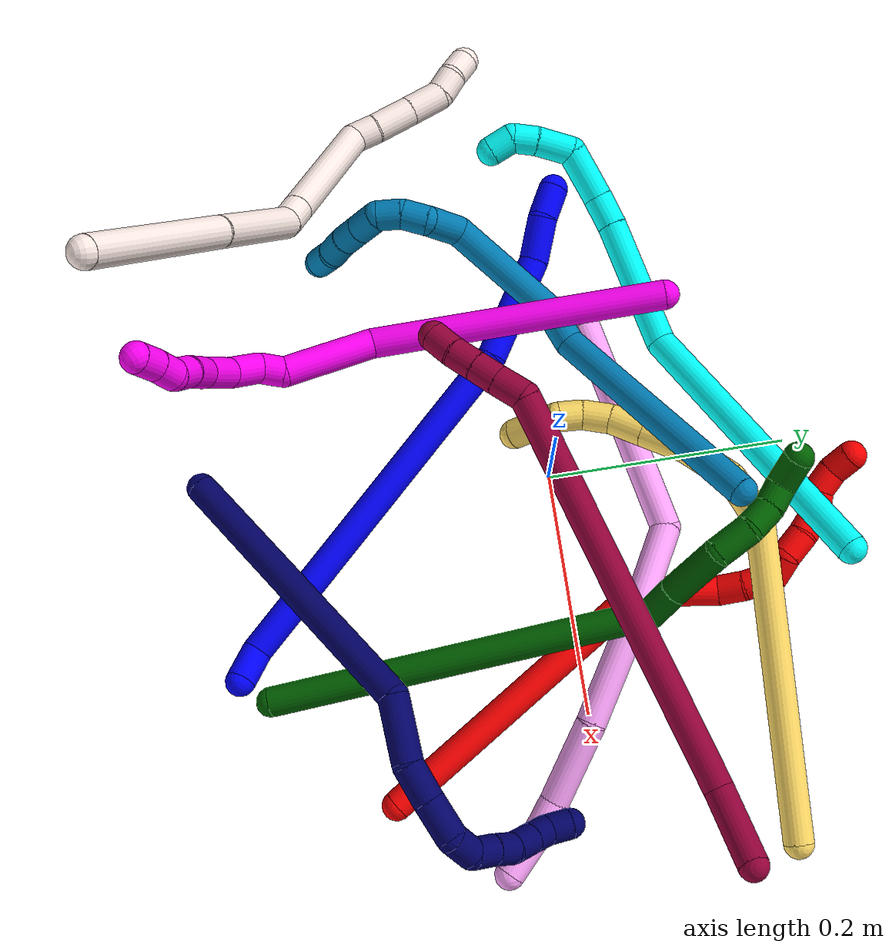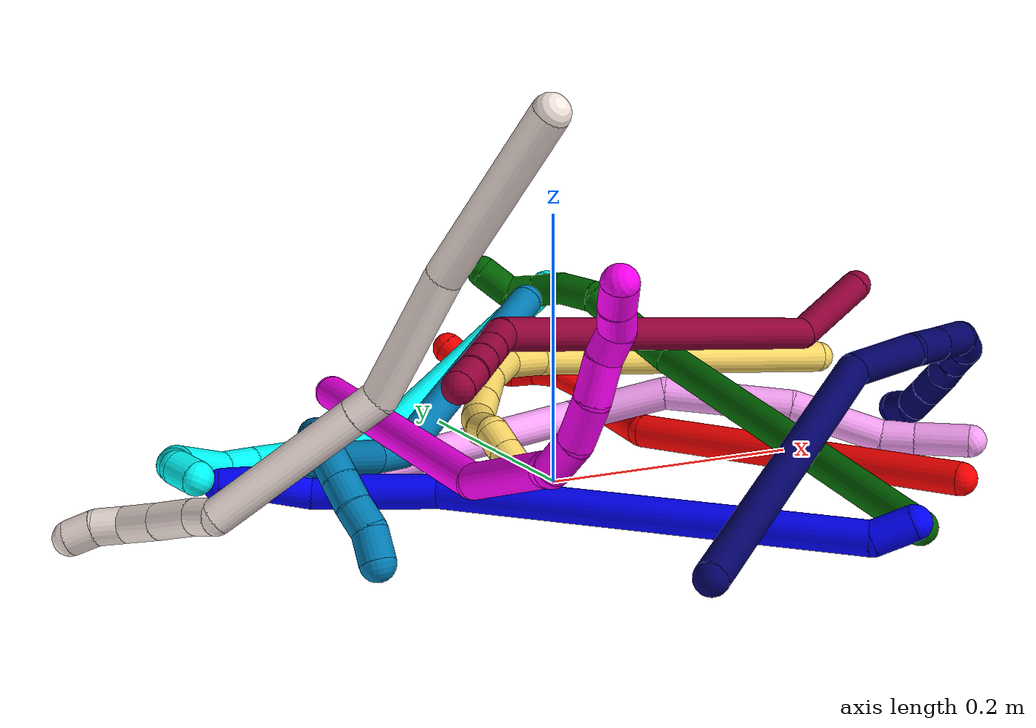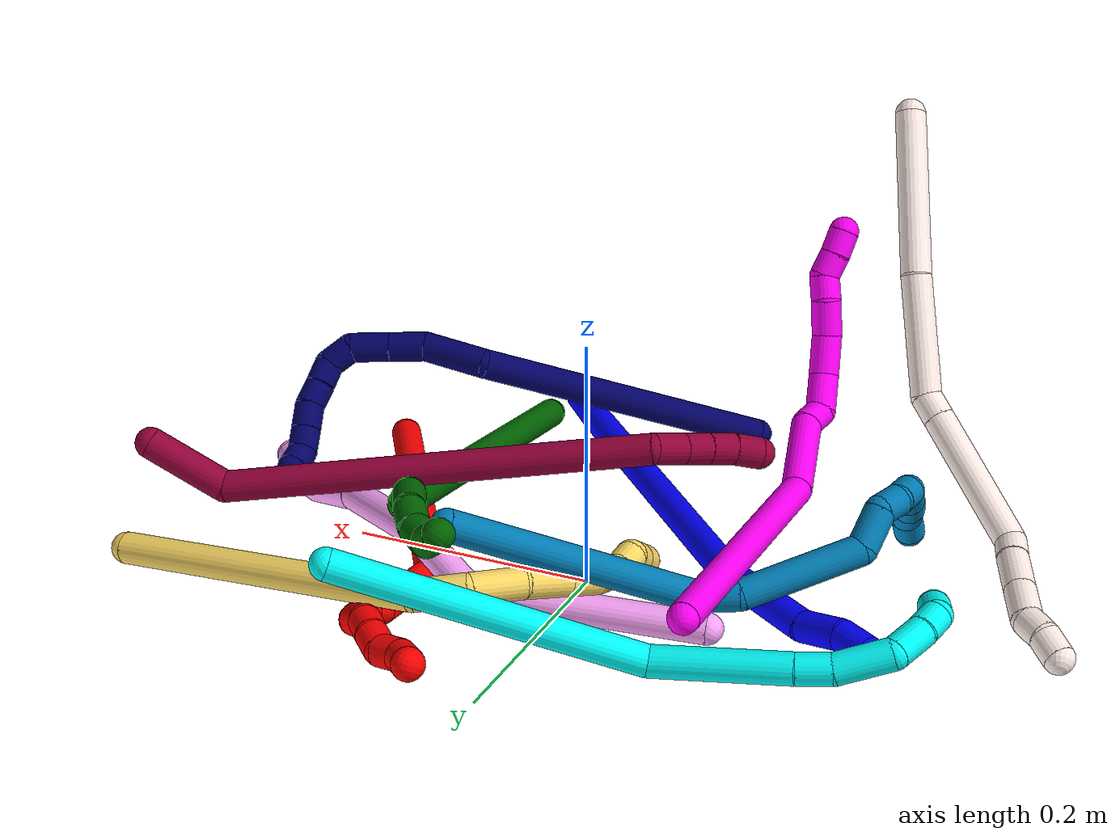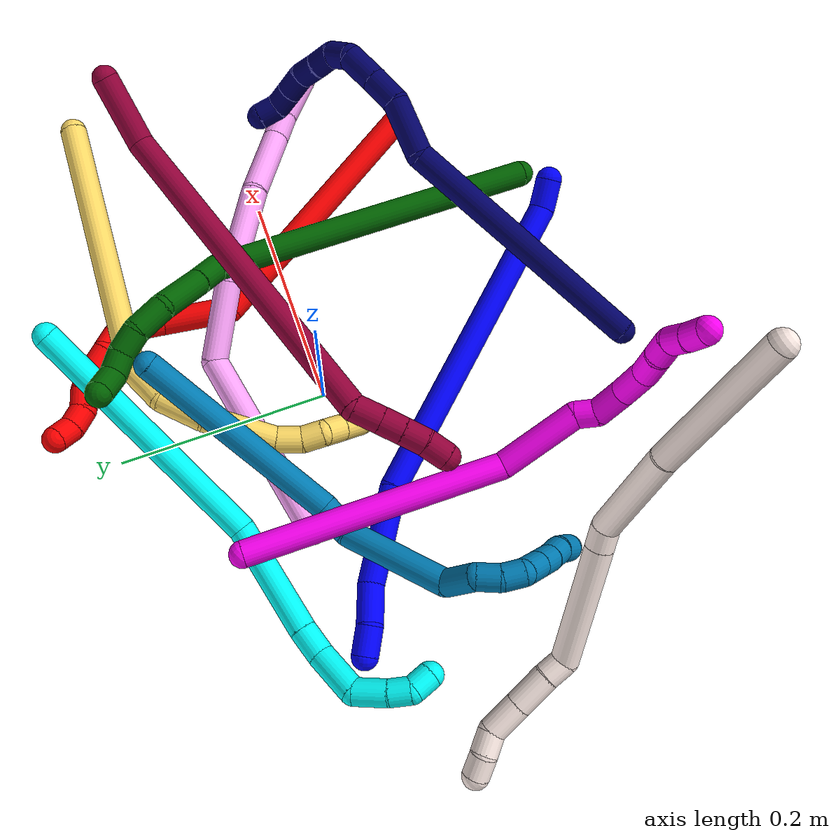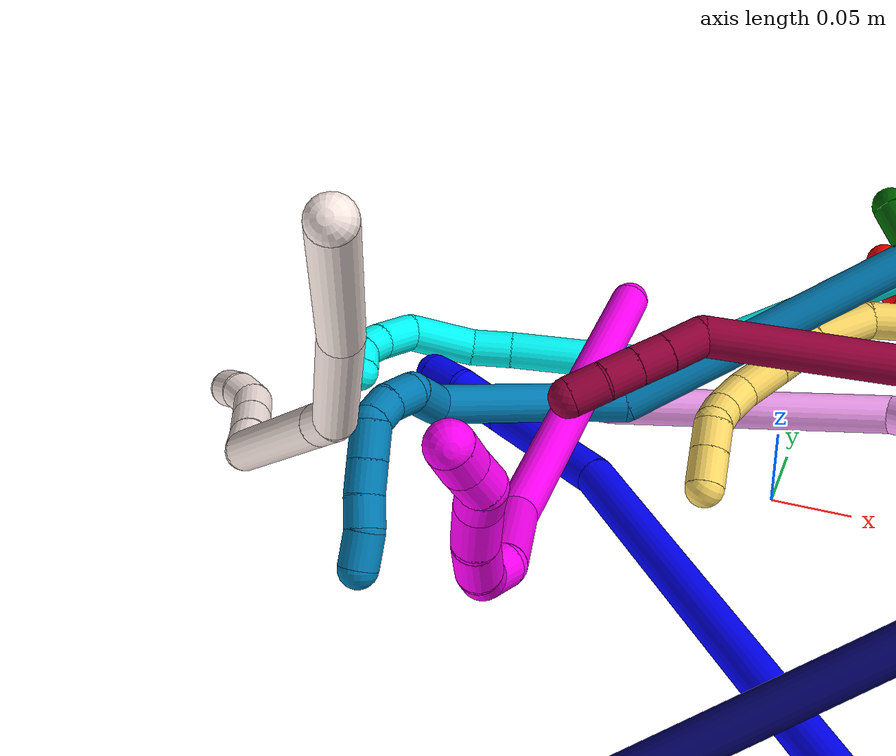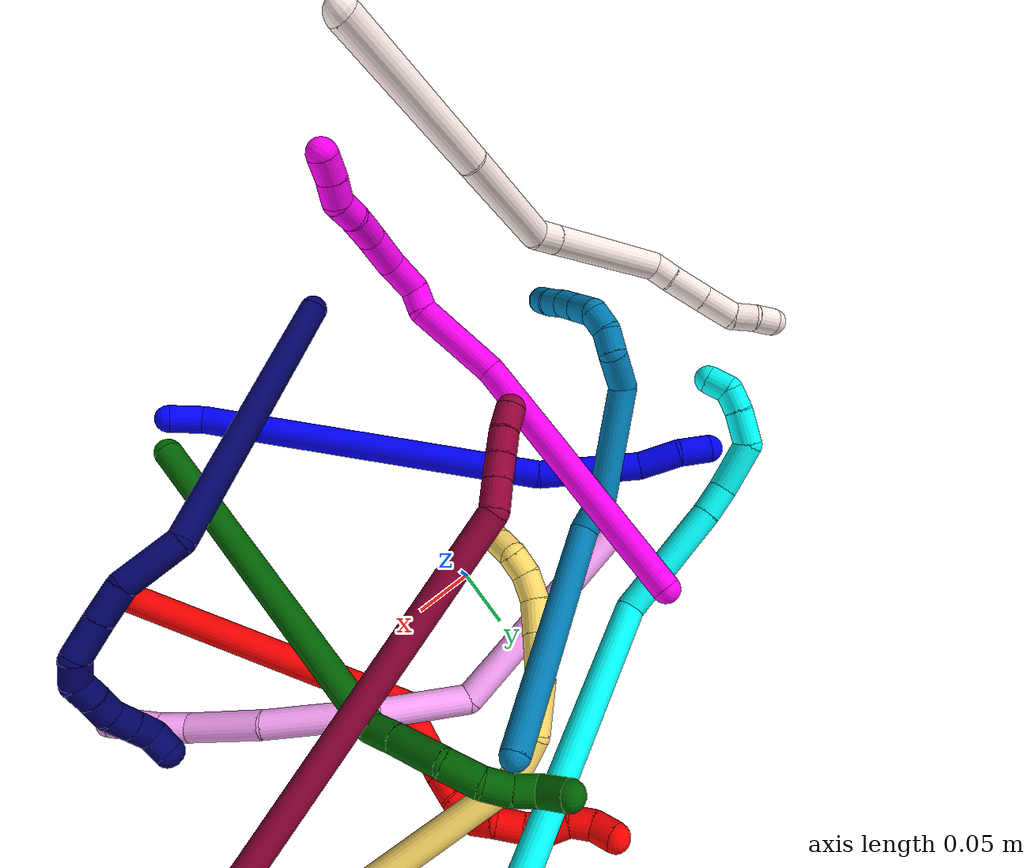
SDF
<sdf version="1.7">
 <world name="default">
  <plugin name="TubeGeneratorPlugin" filename="libtube_generator_plugin.so"/>
  <model name="photoneo_s_sensor">
   <static>1</static>
   <pose>0 0 2 1.57079 1.57079 3.14159</pose>
   <link name="link">
    <inertial><mass>0.1</mass></inertial>
    <sensor name="sensor" type="depth">
     <update_rate>30</update_rate>
     <camera>
      <horizontal_fov>1.22</horizontal_fov>
      <image><width>1920</width><height>1200</height><format>B8G8R8</format></image>
      <clip><near>0.1</near><far>4</far></clip>
      <depth_camera><output>points</output></depth_camera>
     </camera>
     <plugin name="camera_plugin" filename="libgazebo_ros_depth_camera.so">
      <baseline>0.2</baseline>
      <alwaysOn>1</alwaysOn>
      <updateRate>0.0</updateRate>
      <cameraName>camera_ir</cameraName>
      <imageTopicName>/camera/color/image_raw</imageTopicName>
      <cameraInfoTopicName>/camera/color/camera_info</cameraInfoTopicName>
      <depthImageTopicName>/camera/depth/image_raw</depthImageTopicName>
      <depthImageCameraInfoTopicName>/camera/depth/camera_info</depthImageCameraInfoTopicName>
      <pointCloudTopicName>/camera/depth/points</pointCloudTopicName>
      <frameName>fr_optical</frameName>
      <pointCloudCutoff>0.1</pointCloudCutoff>
      <pointCloudCutoffMax>2.0</pointCloudCutoffMax>
      <distortionK1>0</distortionK1>
      <distortionK2>0</distortionK2>
      <distortionK3>0</distortionK3>
      <distortionT1>0</distortionT1>
      <distortionT2>0</distortionT2>
      <CxPrime>0</CxPrime>
      <Cx>0</Cx>
      <Cy>0</Cy>
      <focalLength>0</focalLength>
      <hackBaseline>0</hackBaseline>
     </plugin>
    </sensor>
   </link>
  </model>
  <gravity>0 0 -9.8</gravity>
  <magnetic_field>6e-06 2.3e-05 -4.2e-05</magnetic_field>
  <atmosphere type="adiabatic"/>
  <physics name="default_physics" default="0" type="ode">
   <max_step_size>0.003</max_step_size>
   <real_time_factor>1</real_time_factor>
   <real_time_update_rate>1000</real_time_update_rate>
   <max_contacts>10000</max_contacts>
   <ode>
    <solver>
     <type>quick</type>
     <iters>100</iters>
     <sor>1.3</sor>
     <use_dynamic_moi_rescaling>0</use_dynamic_moi_rescaling>
    </solver>
    <constraints>
     <contact_max_correcting_vel>0</contact_max_correcting_vel>
     <contact_surface_layer>0.001</contact_surface_layer>
     <cfm>0</cfm>
     <erp>0.2</erp>
    </constraints>
   </ode>
  </physics>
  <scene><ambient>0.4 0.4 0.4 1</ambient><background>0.7 0.7 0.7 1</background><shadows>0</shadows></scene>
  <audio><device>default</device></audio>
  <spherical_coordinates>
   <surface_model>EARTH_WGS84</surface_model>
   <latitude_deg>0</latitude_deg>
   <longitude_deg>0</longitude_deg>
   <elevation>0</elevation>
   <heading_deg>0</heading_deg>
  </spherical_coordinates>
  <model name="bin">
   <static>1</static>
   <link name="bottom">
    <collision name="collision-bottom">
     <pose>0 0 -0.01 0 -0 0</pose>
     <geometry><box><size>0.8 0.6 0.02</size></box></geometry>
     <surface>
      <friction><ode><mu>100</mu><mu2>100</mu2></ode></friction>
      <contact><collide_bitmask>65535</collide_bitmask></contact>
     </surface>
    </collision>
   </link>
   <link name="west_wall">
    <collision name="collision-west_wall">
     <pose>-0.41 0 0.1 0 -0 0</pose>
     <geometry><box><size>0.02 0.6 0.2</size></box></geometry>
     <surface>
      <friction><ode><mu>100</mu><mu2>100</mu2></ode></friction>
      <contact><collide_bitmask>65535</collide_bitmask></contact>
     </surface>
    </collision>
   </link>
   <link name="east_wall">
    <collision name="collision-east_wall">
     <pose>0.41 0 0.1 0 -0 0</pose>
     <geometry><box><size>0.02 0.6 0.2</size></box></geometry>
     <surface>
      <friction><ode><mu>100</mu><mu2>100</mu2></ode></friction>
      <contact><collide_bitmask>65535</collide_bitmask></contact>
     </surface>
    </collision>
   </link>
   <link name="south_wall">
    <collision name="collision-south_wall">
     <pose>0 -0.31 0.1 0 -0 0</pose>
     <geometry><box><size>0.8 0.02 0.2</size></box></geometry>
     <surface>
      <friction><ode><mu>100</mu><mu2>100</mu2></ode></friction>
      <contact><collide_bitmask>65535</collide_bitmask></contact>
     </surface>
    </collision>
   </link>
   <link name="north_wall">
    <collision name="collision-north_wall">
     <pose>0 0.31 0.1 0 -0 0</pose>
     <geometry><box><size>0.8 0.02 0.2</size></box></geometry>
     <surface>
      <friction><ode><mu>100</mu><mu2>100</mu2></ode></friction>
      <contact><collide_bitmask>65535</collide_bitmask></contact>
     </surface>
    </collision>
   </link>
  </model>
  <model name="1">
   <static>0</static>
   <link name="1">
    <collision name="collision-cylinder-e_1_1_4">
     <pose>-0.001467 0.002556 -0.014623 -2.96853 -0.098531 1.03367</pose>
     <geometry><cylinder><radius>0.0125</radius><length>0.029834</length></cylinder></geometry>
     <surface>
      <friction><ode><mu>1.16</mu><mu2>1.16</mu2><slip1>0</slip1><slip2>0</slip2></ode></friction>
      <contact><ode><kp>1e+06</kp><kd>1</kd><max_vel>0</max_vel><min_depth>0.001</min_depth></ode></contact>
     </surface>
    </collision>
    <visual name="visual-cylinder-e_1_1_4">
     <pose>-0.001467 0.002556 -0.014623 -2.96853 -0.098531 1.03367</pose>
     <geometry><cylinder><radius>0.0125</radius><length>0.029834</length></cylinder></geometry>
     <material><ambient>0 0 1 1</ambient></material>
    </visual>
    <collision name="collision-cylinder-e_2_4_5">
     <pose>-0.062699 0.083069 -0.15115 -2.57264 -0.391686 1.19224</pose>
     <geometry><cylinder><radius>0.0125</radius><length>0.31311</length></cylinder></geometry>
     <surface>
      <friction><ode><mu>1.16</mu><mu2>1.16</mu2><slip1>0</slip1><slip2>0</slip2></ode></friction>
      <contact><ode><kp>1e+06</kp><kd>1</kd><max_vel>0</max_vel><min_depth>0.001</min_depth></ode></contact>
     </surface>
    </collision>
    <visual name="visual-cylinder-e_2_4_5">
     <pose>-0.062699 0.083069 -0.15115 -2.57264 -0.391686 1.19224</pose>
     <geometry><cylinder><radius>0.0125</radius><length>0.31311</length></cylinder></geometry>
     <material><ambient>0 0 1 1</ambient></material>
    </visual>
    <collision name="collision-cylinder-e_3_5_6">
     <pose>-0.142909 0.172766 -0.312311 -2.851 -0.462811 2.03013</pose>
     <geometry><cylinder><radius>0.0125</radius><length>0.091587</length></cylinder></geometry>
     <surface>
      <friction><ode><mu>1.16</mu><mu2>1.16</mu2><slip1>0</slip1><slip2>0</slip2></ode></friction>
      <contact><ode><kp>1e+06</kp><kd>1</kd><max_vel>0</max_vel><min_depth>0.001</min_depth></ode></contact>
     </surface>
    </collision>
    <visual name="visual-cylinder-e_3_5_6">
     <pose>-0.142909 0.172766 -0.312311 -2.851 -0.462811 2.03013</pose>
     <geometry><cylinder><radius>0.0125</radius><length>0.091587</length></cylinder></geometry>
     <material><ambient>0 0 1 1</ambient></material>
    </visual>
    <collision name="collision-cylinder-e_4_6_7">
     <pose>-0.176053 0.186626 -0.36538 -2.98928 -0.737685 2.75179</pose>
     <geometry><cylinder><radius>0.0125</radius><length>0.037761</length></cylinder></geometry>
     <surface>
      <friction><ode><mu>1.16</mu><mu2>1.16</mu2><slip1>0</slip1><slip2>0</slip2></ode></friction>
      <contact><ode><kp>1e+06</kp><kd>1</kd><max_vel>0</max_vel><min_depth>0.001</min_depth></ode></contact>
     </surface>
    </collision>
    <visual name="visual-cylinder-e_4_6_7">
     <pose>-0.176053 0.186626 -0.36538 -2.98928 -0.737685 2.75179</pose>
     <geometry><cylinder><radius>0.0125</radius><length>0.037761</length></cylinder></geometry>
     <material><ambient>0 0 1 1</ambient></material>
    </visual>
    <collision name="collision-cylinder-e_5_7_2">
     <pose>-0.194797 0.191326 -0.391385 -2.93312 -0.451596 2.28689</pose>
     <geometry><cylinder><radius>0.0125</radius><length>0.027707</length></cylinder></geometry>
     <surface>
      <friction><ode><mu>1.16</mu><mu2>1.16</mu2><slip1>0</slip1><slip2>0</slip2></ode></friction>
      <contact><ode><kp>1e+06</kp><kd>1</kd><max_vel>0</max_vel><min_depth>0.001</min_depth></ode></contact>
     </surface>
    </collision>
    <visual name="visual-cylinder-e_5_7_2">
     <pose>-0.194797 0.191326 -0.391385 -2.93312 -0.451596 2.28689</pose>
     <geometry><cylinder><radius>0.0125</radius><length>0.027707</length></cylinder></geometry>
     <material><ambient>0 0 1 1</ambient></material>
    </visual>
    <collision name="collision-sphere-2">
     <pose>-0.200843 0.193906 -0.40358 0 -0 0</pose>
     <geometry><sphere><radius>0.0125</radius></sphere></geometry>
     <surface>
      <friction><ode><mu>1.16</mu><mu2>1.16</mu2><slip1>0</slip1><slip2>0</slip2></ode></friction>
      <contact><ode><kp>1e+06</kp><kd>1</kd><max_vel>0</max_vel><min_depth>0.001</min_depth></ode></contact>
     </surface>
    </collision>
    <visual name="visual-sphere-2">
     <pose>-0.200843 0.193906 -0.40358 0 -0 0</pose>
     <geometry><sphere><radius>0.0125</radius></sphere></geometry>
     <material><ambient>0 0 1 1</ambient></material>
    </visual>
    <collision name="collision-sphere-7">
     <pose>-0.188751 0.188746 -0.37919 0 -0 0</pose>
     <geometry><sphere><radius>0.0125</radius></sphere></geometry>
     <surface>
      <friction><ode><mu>1.16</mu><mu2>1.16</mu2><slip1>0</slip1><slip2>0</slip2></ode></friction>
      <contact><ode><kp>1e+06</kp><kd>1</kd><max_vel>0</max_vel><min_depth>0.001</min_depth></ode></contact>
     </surface>
    </collision>
    <visual name="visual-sphere-7">
     <pose>-0.188751 0.188746 -0.37919 0 -0 0</pose>
     <geometry><sphere><radius>0.0125</radius></sphere></geometry>
     <material><ambient>0 0 1 1</ambient></material>
    </visual>
    <collision name="collision-sphere-6">
     <pose>-0.163354 0.184506 -0.351569 0 -0 0</pose>
     <geometry><sphere><radius>0.0125</radius></sphere></geometry>
     <surface>
      <friction><ode><mu>1.16</mu><mu2>1.16</mu2><slip1>0</slip1><slip2>0</slip2></ode></friction>
      <contact><ode><kp>1e+06</kp><kd>1</kd><max_vel>0</max_vel><min_depth>0.001</min_depth></ode></contact>
     </surface>
    </collision>
    <visual name="visual-sphere-6">
     <pose>-0.163354 0.184506 -0.351569 0 -0 0</pose>
     <geometry><sphere><radius>0.0125</radius></sphere></geometry>
     <material><ambient>0 0 1 1</ambient></material>
    </visual>
    <collision name="collision-sphere-5">
     <pose>-0.122464 0.161025 -0.273053 0 -0 0</pose>
     <geometry><sphere><radius>0.0125</radius></sphere></geometry>
     <surface>
      <friction><ode><mu>1.16</mu><mu2>1.16</mu2><slip1>0</slip1><slip2>0</slip2></ode></friction>
      <contact><ode><kp>1e+06</kp><kd>1</kd><max_vel>0</max_vel><min_depth>0.001</min_depth></ode></contact>
     </surface>
    </collision>
    <visual name="visual-sphere-5">
     <pose>-0.122464 0.161025 -0.273053 0 -0 0</pose>
     <geometry><sphere><radius>0.0125</radius></sphere></geometry>
     <material><ambient>0 0 1 1</ambient></material>
    </visual>
    <collision name="collision-sphere-1">
     <geometry><sphere><radius>0.0125</radius></sphere></geometry>
     <surface>
      <friction><ode><mu>1.16</mu><mu2>1.16</mu2><slip1>0</slip1><slip2>0</slip2></ode></friction>
      <contact><ode><kp>1e+06</kp><kd>1</kd><max_vel>0</max_vel><min_depth>0.001</min_depth></ode></contact>
     </surface>
    </collision>
    <visual name="visual-sphere-1">
     <geometry><sphere><radius>0.0125</radius></sphere></geometry>
     <material><ambient>0 0 1 1</ambient></material>
    </visual>
    <collision name="collision-sphere-4">
     <pose>-0.002935 0.005113 -0.029246 0 -0 0</pose>
     <geometry><sphere><radius>0.0125</radius></sphere></geometry>
     <surface>
      <friction><ode><mu>1.16</mu><mu2>1.16</mu2><slip1>0</slip1><slip2>0</slip2></ode></friction>
      <contact><ode><kp>1e+06</kp><kd>1</kd><max_vel>0</max_vel><min_depth>0.001</min_depth></ode></contact>
     </surface>
    </collision>
    <visual name="visual-sphere-4">
     <pose>-0.002935 0.005113 -0.029246 0 -0 0</pose>
     <geometry><sphere><radius>0.0125</radius></sphere></geometry>
     <material><ambient>0 0 1 1</ambient></material>
    </visual>
    <inertial>
     <pose>-0.089619 0.108515 -0.202016 0 -0 0</pose>
     <mass>0.5</mass>
     <inertia>
      <ixx>0.0031</ixx>
      <ixy>0</ixy>
      <ixz>0</ixz>
      <iyy>0.002017</iyy>
      <iyz>0</iyz>
      <izz>-0.000314</izz>
     </inertia>
    </inertial>
   </link>
   <pose>0.128806 -0.276052 0.023398 0.375192 0.970139 0.023917</pose>
  </model>
  <model name="2">
   <static>0</static>
   <link name="2">
    <collision name="collision-cylinder-e_1_1_4">
     <pose>-0.067282 0.101633 -0.0497 -2.02562 -0.536521 0.829711</pose>
     <geometry><cylinder><radius>0.0125</radius><length>0.263259</length></cylinder></geometry>
     <surface>
      <friction><ode><mu>1.16</mu><mu2>1.16</mu2><slip1>0</slip1><slip2>0</slip2></ode></friction>
      <contact><ode><kp>1e+06</kp><kd>1</kd><max_vel>0</max_vel><min_depth>0.001</min_depth></ode></contact>
     </surface>
    </collision>
    <visual name="visual-cylinder-e_1_1_4">
     <pose>-0.067282 0.101633 -0.0497 -2.02562 -0.536521 0.829711</pose>
     <geometry><cylinder><radius>0.0125</radius><length>0.263259</length></cylinder></geometry>
     <material><ambient>1 0 0 1</ambient></material>
    </visual>
    <collision name="collision-cylinder-e_2_4_5">
     <pose>-0.129361 0.230539 -0.117364 -2.15326 0.158013 -0.291817</pose>
     <geometry><cylinder><radius>0.0125</radius><length>0.066138</length></cylinder></geometry>
     <surface>
      <friction><ode><mu>1.16</mu><mu2>1.16</mu2><slip1>0</slip1><slip2>0</slip2></ode></friction>
      <contact><ode><kp>1e+06</kp><kd>1</kd><max_vel>0</max_vel><min_depth>0.001</min_depth></ode></contact>
     </surface>
    </collision>
    <visual name="visual-cylinder-e_2_4_5">
     <pose>-0.129361 0.230539 -0.117364 -2.15326 0.158013 -0.291817</pose>
     <geometry><cylinder><radius>0.0125</radius><length>0.066138</length></cylinder></geometry>
     <material><ambient>1 0 0 1</ambient></material>
    </visual>
    <collision name="collision-cylinder-e_3_5_6">
     <pose>-0.123428 0.269037 -0.137258 -1.741 0.063919 -0.075831</pose>
     <geometry><cylinder><radius>0.0125</radius><length>0.022827</length></cylinder></geometry>
     <surface>
      <friction><ode><mu>1.16</mu><mu2>1.16</mu2><slip1>0</slip1><slip2>0</slip2></ode></friction>
      <contact><ode><kp>1e+06</kp><kd>1</kd><max_vel>0</max_vel><min_depth>0.001</min_depth></ode></contact>
     </surface>
    </collision>
    <visual name="visual-cylinder-e_3_5_6">
     <pose>-0.123428 0.269037 -0.137258 -1.741 0.063919 -0.075831</pose>
     <geometry><cylinder><radius>0.0125</radius><length>0.022827</length></cylinder></geometry>
     <material><ambient>1 0 0 1</ambient></material>
    </visual>
    <collision name="collision-cylinder-e_4_6_7">
     <pose>-0.123754 0.291784 -0.142481 -1.84923 -0.087812 0.116374</pose>
     <geometry><cylinder><radius>0.0125</radius><length>0.024058</length></cylinder></geometry>
     <surface>
      <friction><ode><mu>1.16</mu><mu2>1.16</mu2><slip1>0</slip1><slip2>0</slip2></ode></friction>
      <contact><ode><kp>1e+06</kp><kd>1</kd><max_vel>0</max_vel><min_depth>0.001</min_depth></ode></contact>
     </surface>
    </collision>
    <visual name="visual-cylinder-e_4_6_7">
     <pose>-0.123754 0.291784 -0.142481 -1.84923 -0.087812 0.116374</pose>
     <geometry><cylinder><radius>0.0125</radius><length>0.024058</length></cylinder></geometry>
     <material><ambient>1 0 0 1</ambient></material>
    </visual>
    <collision name="collision-cylinder-e_5_7_8">
     <pose>-0.131424 0.311554 -0.14424 -1.38688 -0.667612 0.561236</pose>
     <geometry><cylinder><radius>0.0125</radius><length>0.021368</length></cylinder></geometry>
     <surface>
      <friction><ode><mu>1.16</mu><mu2>1.16</mu2><slip1>0</slip1><slip2>0</slip2></ode></friction>
      <contact><ode><kp>1e+06</kp><kd>1</kd><max_vel>0</max_vel><min_depth>0.001</min_depth></ode></contact>
     </surface>
    </collision>
    <visual name="visual-cylinder-e_5_7_8">
     <pose>-0.131424 0.311554 -0.14424 -1.38688 -0.667612 0.561236</pose>
     <geometry><cylinder><radius>0.0125</radius><length>0.021368</length></cylinder></geometry>
     <material><ambient>1 0 0 1</ambient></material>
    </visual>
    <collision name="collision-cylinder-e_6_8_9">
     <pose>-0.145133 0.327549 -0.145998 -1.97273 -0.700375 1.00895</pose>
     <geometry><cylinder><radius>0.0125</radius><length>0.022017</length></cylinder></geometry>
     <surface>
      <friction><ode><mu>1.16</mu><mu2>1.16</mu2><slip1>0</slip1><slip2>0</slip2></ode></friction>
      <contact><ode><kp>1e+06</kp><kd>1</kd><max_vel>0</max_vel><min_depth>0.001</min_depth></ode></contact>
     </surface>
    </collision>
    <visual name="visual-cylinder-e_6_8_9">
     <pose>-0.145133 0.327549 -0.145998 -1.97273 -0.700375 1.00895</pose>
     <geometry><cylinder><radius>0.0125</radius><length>0.022017</length></cylinder></geometry>
     <material><ambient>1 0 0 1</ambient></material>
    </visual>
    <collision name="collision-cylinder-e_7_9_10">
     <pose>-0.159547 0.340988 -0.153201 -2.1727 -0.814339 1.373</pose>
     <geometry><cylinder><radius>0.0125</radius><length>0.020126</length></cylinder></geometry>
     <surface>
      <friction><ode><mu>1.16</mu><mu2>1.16</mu2><slip1>0</slip1><slip2>0</slip2></ode></friction>
      <contact><ode><kp>1e+06</kp><kd>1</kd><max_vel>0</max_vel><min_depth>0.001</min_depth></ode></contact>
     </surface>
    </collision>
    <visual name="visual-cylinder-e_7_9_10">
     <pose>-0.159547 0.340988 -0.153201 -2.1727 -0.814339 1.373</pose>
     <geometry><cylinder><radius>0.0125</radius><length>0.020126</length></cylinder></geometry>
     <material><ambient>1 0 0 1</ambient></material>
    </visual>
    <collision name="collision-cylinder-e_8_10_11">
     <pose>-0.175999 0.350679 -0.156194 -1.34517 -1.1487 0.951799</pose>
     <geometry><cylinder><radius>0.0125</radius><length>0.020023</length></cylinder></geometry>
     <surface>
      <friction><ode><mu>1.16</mu><mu2>1.16</mu2><slip1>0</slip1><slip2>0</slip2></ode></friction>
      <contact><ode><kp>1e+06</kp><kd>1</kd><max_vel>0</max_vel><min_depth>0.001</min_depth></ode></contact>
     </surface>
    </collision>
    <visual name="visual-cylinder-e_8_10_11">
     <pose>-0.175999 0.350679 -0.156194 -1.34517 -1.1487 0.951799</pose>
     <geometry><cylinder><radius>0.0125</radius><length>0.020023</length></cylinder></geometry>
     <material><ambient>1 0 0 1</ambient></material>
    </visual>
    <collision name="collision-cylinder-e_9_11_12">
     <pose>-0.191689 0.362199 -0.156566 -1.74047 -0.70979 0.828131</pose>
     <geometry><cylinder><radius>0.0125</radius><length>0.020126</length></cylinder></geometry>
     <surface>
      <friction><ode><mu>1.16</mu><mu2>1.16</mu2><slip1>0</slip1><slip2>0</slip2></ode></friction>
      <contact><ode><kp>1e+06</kp><kd>1</kd><max_vel>0</max_vel><min_depth>0.001</min_depth></ode></contact>
     </surface>
    </collision>
    <visual name="visual-cylinder-e_9_11_12">
     <pose>-0.191689 0.362199 -0.156566 -1.74047 -0.70979 0.828131</pose>
     <geometry><cylinder><radius>0.0125</radius><length>0.020126</length></cylinder></geometry>
     <material><ambient>1 0 0 1</ambient></material>
    </visual>
    <collision name="collision-cylinder-e_10_12_2">
     <pose>-0.20158 0.379156 -0.157157 -1.49701 -0.338739 0.315034</pose>
     <geometry><cylinder><radius>0.0125</radius><length>0.020057</length></cylinder></geometry>
     <surface>
      <friction><ode><mu>1.16</mu><mu2>1.16</mu2><slip1>0</slip1><slip2>0</slip2></ode></friction>
      <contact><ode><kp>1e+06</kp><kd>1</kd><max_vel>0</max_vel><min_depth>0.001</min_depth></ode></contact>
     </surface>
    </collision>
    <visual name="visual-cylinder-e_10_12_2">
     <pose>-0.20158 0.379156 -0.157157 -1.49701 -0.338739 0.315034</pose>
     <geometry><cylinder><radius>0.0125</radius><length>0.020057</length></cylinder></geometry>
     <material><ambient>1 0 0 1</ambient></material>
    </visual>
    <collision name="collision-sphere-2">
     <pose>-0.204912 0.388588 -0.15646 0 -0 0</pose>
     <geometry><sphere><radius>0.0125</radius></sphere></geometry>
     <surface>
      <friction><ode><mu>1.16</mu><mu2>1.16</mu2><slip1>0</slip1><slip2>0</slip2></ode></friction>
      <contact><ode><kp>1e+06</kp><kd>1</kd><max_vel>0</max_vel><min_depth>0.001</min_depth></ode></contact>
     </surface>
    </collision>
    <visual name="visual-sphere-2">
     <pose>-0.204912 0.388588 -0.15646 0 -0 0</pose>
     <geometry><sphere><radius>0.0125</radius></sphere></geometry>
     <material><ambient>1 0 0 1</ambient></material>
    </visual>
    <collision name="collision-sphere-12">
     <pose>-0.198247 0.369723 -0.157855 0 -0 0</pose>
     <geometry><sphere><radius>0.0125</radius></sphere></geometry>
     <surface>
      <friction><ode><mu>1.16</mu><mu2>1.16</mu2><slip1>0</slip1><slip2>0</slip2></ode></friction>
      <contact><ode><kp>1e+06</kp><kd>1</kd><max_vel>0</max_vel><min_depth>0.001</min_depth></ode></contact>
     </surface>
    </collision>
    <visual name="visual-sphere-12">
     <pose>-0.198247 0.369723 -0.157855 0 -0 0</pose>
     <geometry><sphere><radius>0.0125</radius></sphere></geometry>
     <material><ambient>1 0 0 1</ambient></material>
    </visual>
    <collision name="collision-sphere-11">
     <pose>-0.185131 0.354676 -0.155277 0 -0 0</pose>
     <geometry><sphere><radius>0.0125</radius></sphere></geometry>
     <surface>
      <friction><ode><mu>1.16</mu><mu2>1.16</mu2><slip1>0</slip1><slip2>0</slip2></ode></friction>
      <contact><ode><kp>1e+06</kp><kd>1</kd><max_vel>0</max_vel><min_depth>0.001</min_depth></ode></contact>
     </surface>
    </collision>
    <visual name="visual-sphere-11">
     <pose>-0.185131 0.354676 -0.155277 0 -0 0</pose>
     <geometry><sphere><radius>0.0125</radius></sphere></geometry>
     <material><ambient>1 0 0 1</ambient></material>
    </visual>
    <collision name="collision-sphere-10">
     <pose>-0.166866 0.346681 -0.157112 0 -0 0</pose>
     <geometry><sphere><radius>0.0125</radius></sphere></geometry>
     <surface>
      <friction><ode><mu>1.16</mu><mu2>1.16</mu2><slip1>0</slip1><slip2>0</slip2></ode></friction>
      <contact><ode><kp>1e+06</kp><kd>1</kd><max_vel>0</max_vel><min_depth>0.001</min_depth></ode></contact>
     </surface>
    </collision>
    <visual name="visual-sphere-10">
     <pose>-0.166866 0.346681 -0.157112 0 -0 0</pose>
     <geometry><sphere><radius>0.0125</radius></sphere></geometry>
     <material><ambient>1 0 0 1</ambient></material>
    </visual>
    <collision name="collision-sphere-9">
     <pose>-0.152229 0.335295 -0.149291 0 -0 0</pose>
     <geometry><sphere><radius>0.0125</radius></sphere></geometry>
     <surface>
      <friction><ode><mu>1.16</mu><mu2>1.16</mu2><slip1>0</slip1><slip2>0</slip2></ode></friction>
      <contact><ode><kp>1e+06</kp><kd>1</kd><max_vel>0</max_vel><min_depth>0.001</min_depth></ode></contact>
     </surface>
    </collision>
    <visual name="visual-sphere-9">
     <pose>-0.152229 0.335295 -0.149291 0 -0 0</pose>
     <geometry><sphere><radius>0.0125</radius></sphere></geometry>
     <material><ambient>1 0 0 1</ambient></material>
    </visual>
    <collision name="collision-sphere-4">
     <pose>-0.134565 0.203267 -0.0994 0 -0 0</pose>
     <geometry><sphere><radius>0.0125</radius></sphere></geometry>
     <surface>
      <friction><ode><mu>1.16</mu><mu2>1.16</mu2><slip1>0</slip1><slip2>0</slip2></ode></friction>
      <contact><ode><kp>1e+06</kp><kd>1</kd><max_vel>0</max_vel><min_depth>0.001</min_depth></ode></contact>
     </surface>
    </collision>
    <visual name="visual-sphere-4">
     <pose>-0.134565 0.203267 -0.0994 0 -0 0</pose>
     <geometry><sphere><radius>0.0125</radius></sphere></geometry>
     <material><ambient>1 0 0 1</ambient></material>
    </visual>
    <collision name="collision-sphere-1">
     <geometry><sphere><radius>0.0125</radius></sphere></geometry>
     <surface>
      <friction><ode><mu>1.16</mu><mu2>1.16</mu2><slip1>0</slip1><slip2>0</slip2></ode></friction>
      <contact><ode><kp>1e+06</kp><kd>1</kd><max_vel>0</max_vel><min_depth>0.001</min_depth></ode></contact>
     </surface>
    </collision>
    <visual name="visual-sphere-1">
     <geometry><sphere><radius>0.0125</radius></sphere></geometry>
     <material><ambient>1 0 0 1</ambient></material>
    </visual>
    <collision name="collision-sphere-8">
     <pose>-0.138038 0.319802 -0.142705 0 -0 0</pose>
     <geometry><sphere><radius>0.0125</radius></sphere></geometry>
     <surface>
      <friction><ode><mu>1.16</mu><mu2>1.16</mu2><slip1>0</slip1><slip2>0</slip2></ode></friction>
      <contact><ode><kp>1e+06</kp><kd>1</kd><max_vel>0</max_vel><min_depth>0.001</min_depth></ode></contact>
     </surface>
    </collision>
    <visual name="visual-sphere-8">
     <pose>-0.138038 0.319802 -0.142705 0 -0 0</pose>
     <geometry><sphere><radius>0.0125</radius></sphere></geometry>
     <material><ambient>1 0 0 1</ambient></material>
    </visual>
    <collision name="collision-sphere-5">
     <pose>-0.124157 0.257812 -0.135329 0 -0 0</pose>
     <geometry><sphere><radius>0.0125</radius></sphere></geometry>
     <surface>
      <friction><ode><mu>1.16</mu><mu2>1.16</mu2><slip1>0</slip1><slip2>0</slip2></ode></friction>
      <contact><ode><kp>1e+06</kp><kd>1</kd><max_vel>0</max_vel><min_depth>0.001</min_depth></ode></contact>
     </surface>
    </collision>
    <visual name="visual-sphere-5">
     <pose>-0.124157 0.257812 -0.135329 0 -0 0</pose>
     <geometry><sphere><radius>0.0125</radius></sphere></geometry>
     <material><ambient>1 0 0 1</ambient></material>
    </visual>
    <collision name="collision-sphere-6">
     <pose>-0.122699 0.280263 -0.139187 0 -0 0</pose>
     <geometry><sphere><radius>0.0125</radius></sphere></geometry>
     <surface>
      <friction><ode><mu>1.16</mu><mu2>1.16</mu2><slip1>0</slip1><slip2>0</slip2></ode></friction>
      <contact><ode><kp>1e+06</kp><kd>1</kd><max_vel>0</max_vel><min_depth>0.001</min_depth></ode></contact>
     </surface>
    </collision>
    <visual name="visual-sphere-6">
     <pose>-0.122699 0.280263 -0.139187 0 -0 0</pose>
     <geometry><sphere><radius>0.0125</radius></sphere></geometry>
     <material><ambient>1 0 0 1</ambient></material>
    </visual>
    <collision name="collision-sphere-7">
     <pose>-0.124809 0.303305 -0.145774 0 -0 0</pose>
     <geometry><sphere><radius>0.0125</radius></sphere></geometry>
     <surface>
      <friction><ode><mu>1.16</mu><mu2>1.16</mu2><slip1>0</slip1><slip2>0</slip2></ode></friction>
      <contact><ode><kp>1e+06</kp><kd>1</kd><max_vel>0</max_vel><min_depth>0.001</min_depth></ode></contact>
     </surface>
    </collision>
    <visual name="visual-sphere-7">
     <pose>-0.124809 0.303305 -0.145774 0 -0 0</pose>
     <geometry><sphere><radius>0.0125</radius></sphere></geometry>
     <material><ambient>1 0 0 1</ambient></material>
    </visual>
    <inertial>
     <pose>-0.105406 0.195624 -0.092436 0 -0 0</pose>
     <mass>0.5</mass>
     <inertia>
      <ixx>0.001873</ixx>
      <ixy>0</ixy>
      <ixz>0</ixz>
      <iyy>0.001053</iyy>
      <iyz>0</iyz>
      <izz>-0.000442</izz>
     </inertia>
    </inertial>
   </link>
   <pose>0.247223 -0.165599 0.011497 0.541978 -0.136553 0.017066</pose>
  </model>
  <model name="3">
   <static>0</static>
   <link name="3">
    <collision name="collision-cylinder-e_1_1_4">
     <pose>-0.067639 -0.033608 -0.097127 2.80847 -0.582058 -2.11869</pose>
     <geometry><cylinder><radius>0.0125</radius><length>0.246075</length></cylinder></geometry>
     <surface>
      <friction><ode><mu>1.16</mu><mu2>1.16</mu2><slip1>0</slip1><slip2>0</slip2></ode></friction>
      <contact><ode><kp>1e+06</kp><kd>1</kd><max_vel>0</max_vel><min_depth>0.001</min_depth></ode></contact>
     </surface>
    </collision>
    <visual name="visual-cylinder-e_1_1_4">
     <pose>-0.067639 -0.033608 -0.097127 2.80847 -0.582058 -2.11869</pose>
     <geometry><cylinder><radius>0.0125</radius><length>0.246075</length></cylinder></geometry>
     <material><ambient>0.003922 1 0.996078 1</ambient></material>
    </visual>
    <collision name="collision-cylinder-e_2_4_5">
     <pose>-0.182653 -0.074121 -0.219384 2.87343 -1.06787 -2.69296</pose>
     <geometry><cylinder><radius>0.0125</radius><length>0.10814</length></cylinder></geometry>
     <surface>
      <friction><ode><mu>1.16</mu><mu2>1.16</mu2><slip1>0</slip1><slip2>0</slip2></ode></friction>
      <contact><ode><kp>1e+06</kp><kd>1</kd><max_vel>0</max_vel><min_depth>0.001</min_depth></ode></contact>
     </surface>
    </collision>
    <visual name="visual-cylinder-e_2_4_5">
     <pose>-0.182653 -0.074121 -0.219384 2.87343 -1.06787 -2.69296</pose>
     <geometry><cylinder><radius>0.0125</radius><length>0.10814</length></cylinder></geometry>
     <material><ambient>0.003922 1 0.996078 1</ambient></material>
    </visual>
    <collision name="collision-cylinder-e_3_5_6">
     <pose>-0.241983 -0.083873 -0.250998 2.72779 -1.036 -2.4358</pose>
     <geometry><cylinder><radius>0.0125</radius><length>0.02779</length></cylinder></geometry>
     <surface>
      <friction><ode><mu>1.16</mu><mu2>1.16</mu2><slip1>0</slip1><slip2>0</slip2></ode></friction>
      <contact><ode><kp>1e+06</kp><kd>1</kd><max_vel>0</max_vel><min_depth>0.001</min_depth></ode></contact>
     </surface>
    </collision>
    <visual name="visual-cylinder-e_3_5_6">
     <pose>-0.241983 -0.083873 -0.250998 2.72779 -1.036 -2.4358</pose>
     <geometry><cylinder><radius>0.0125</radius><length>0.02779</length></cylinder></geometry>
     <material><ambient>0.003922 1 0.996078 1</ambient></material>
    </visual>
    <collision name="collision-cylinder-e_4_6_7">
     <pose>-0.27456 -0.094025 -0.262818 2.20171 -1.15743 -1.81999</pose>
     <geometry><cylinder><radius>0.0125</radius><length>0.045038</length></cylinder></geometry>
     <surface>
      <friction><ode><mu>1.16</mu><mu2>1.16</mu2><slip1>0</slip1><slip2>0</slip2></ode></friction>
      <contact><ode><kp>1e+06</kp><kd>1</kd><max_vel>0</max_vel><min_depth>0.001</min_depth></ode></contact>
     </surface>
    </collision>
    <visual name="visual-cylinder-e_4_6_7">
     <pose>-0.27456 -0.094025 -0.262818 2.20171 -1.15743 -1.81999</pose>
     <geometry><cylinder><radius>0.0125</radius><length>0.045038</length></cylinder></geometry>
     <material><ambient>0.003922 1 0.996078 1</ambient></material>
    </visual>
    <collision name="collision-cylinder-e_5_7_8">
     <pose>-0.301739 -0.115309 -0.271255 1.78912 -0.429395 -0.530663</pose>
     <geometry><cylinder><radius>0.0125</radius><length>0.031498</length></cylinder></geometry>
     <surface>
      <friction><ode><mu>1.16</mu><mu2>1.16</mu2><slip1>0</slip1><slip2>0</slip2></ode></friction>
      <contact><ode><kp>1e+06</kp><kd>1</kd><max_vel>0</max_vel><min_depth>0.001</min_depth></ode></contact>
     </surface>
    </collision>
    <visual name="visual-cylinder-e_5_7_8">
     <pose>-0.301739 -0.115309 -0.271255 1.78912 -0.429395 -0.530663</pose>
     <geometry><cylinder><radius>0.0125</radius><length>0.031498</length></cylinder></geometry>
     <material><ambient>0.003922 1 0.996078 1</ambient></material>
    </visual>
    <collision name="collision-cylinder-e_6_8_9">
     <pose>-0.311129 -0.139177 -0.276027 1.73813 -0.275344 -0.324936</pose>
     <geometry><cylinder><radius>0.0125</radius><length>0.020843</length></cylinder></geometry>
     <surface>
      <friction><ode><mu>1.16</mu><mu2>1.16</mu2><slip1>0</slip1><slip2>0</slip2></ode></friction>
      <contact><ode><kp>1e+06</kp><kd>1</kd><max_vel>0</max_vel><min_depth>0.001</min_depth></ode></contact>
     </surface>
    </collision>
    <visual name="visual-cylinder-e_6_8_9">
     <pose>-0.311129 -0.139177 -0.276027 1.73813 -0.275344 -0.324936</pose>
     <geometry><cylinder><radius>0.0125</radius><length>0.020843</length></cylinder></geometry>
     <material><ambient>0.003922 1 0.996078 1</ambient></material>
    </visual>
    <collision name="collision-cylinder-e_7_9_2">
     <pose>-0.309925 -0.158369 -0.279546 1.76702 0.402464 0.487197</pose>
     <geometry><cylinder><radius>0.0125</radius><length>0.020616</length></cylinder></geometry>
     <surface>
      <friction><ode><mu>1.16</mu><mu2>1.16</mu2><slip1>0</slip1><slip2>0</slip2></ode></friction>
      <contact><ode><kp>1e+06</kp><kd>1</kd><max_vel>0</max_vel><min_depth>0.001</min_depth></ode></contact>
     </surface>
    </collision>
    <visual name="visual-cylinder-e_7_9_2">
     <pose>-0.309925 -0.158369 -0.279546 1.76702 0.402464 0.487197</pose>
     <geometry><cylinder><radius>0.0125</radius><length>0.020616</length></cylinder></geometry>
     <material><ambient>0.003922 1 0.996078 1</ambient></material>
    </visual>
    <collision name="collision-sphere-2">
     <pose>-0.305887 -0.167671 -0.281395 0 -0 0</pose>
     <geometry><sphere><radius>0.0125</radius></sphere></geometry>
     <surface>
      <friction><ode><mu>1.16</mu><mu2>1.16</mu2><slip1>0</slip1><slip2>0</slip2></ode></friction>
      <contact><ode><kp>1e+06</kp><kd>1</kd><max_vel>0</max_vel><min_depth>0.001</min_depth></ode></contact>
     </surface>
    </collision>
    <visual name="visual-sphere-2">
     <pose>-0.305887 -0.167671 -0.281395 0 -0 0</pose>
     <geometry><sphere><radius>0.0125</radius></sphere></geometry>
     <material><ambient>0.003922 1 0.996078 1</ambient></material>
    </visual>
    <collision name="collision-sphere-9">
     <pose>-0.313962 -0.149066 -0.277697 0 -0 0</pose>
     <geometry><sphere><radius>0.0125</radius></sphere></geometry>
     <surface>
      <friction><ode><mu>1.16</mu><mu2>1.16</mu2><slip1>0</slip1><slip2>0</slip2></ode></friction>
      <contact><ode><kp>1e+06</kp><kd>1</kd><max_vel>0</max_vel><min_depth>0.001</min_depth></ode></contact>
     </surface>
    </collision>
    <visual name="visual-sphere-9">
     <pose>-0.313962 -0.149066 -0.277697 0 -0 0</pose>
     <geometry><sphere><radius>0.0125</radius></sphere></geometry>
     <material><ambient>0.003922 1 0.996078 1</ambient></material>
    </visual>
    <collision name="collision-sphere-4">
     <pose>-0.135278 -0.067215 -0.194254 0 -0 0</pose>
     <geometry><sphere><radius>0.0125</radius></sphere></geometry>
     <surface>
      <friction><ode><mu>1.16</mu><mu2>1.16</mu2><slip1>0</slip1><slip2>0</slip2></ode></friction>
      <contact><ode><kp>1e+06</kp><kd>1</kd><max_vel>0</max_vel><min_depth>0.001</min_depth></ode></contact>
     </surface>
    </collision>
    <visual name="visual-sphere-4">
     <pose>-0.135278 -0.067215 -0.194254 0 -0 0</pose>
     <geometry><sphere><radius>0.0125</radius></sphere></geometry>
     <material><ambient>0.003922 1 0.996078 1</ambient></material>
    </visual>
    <collision name="collision-sphere-1">
     <geometry><sphere><radius>0.0125</radius></sphere></geometry>
     <surface>
      <friction><ode><mu>1.16</mu><mu2>1.16</mu2><slip1>0</slip1><slip2>0</slip2></ode></friction>
      <contact><ode><kp>1e+06</kp><kd>1</kd><max_vel>0</max_vel><min_depth>0.001</min_depth></ode></contact>
     </surface>
    </collision>
    <visual name="visual-sphere-1">
     <geometry><sphere><radius>0.0125</radius></sphere></geometry>
     <material><ambient>0.003922 1 0.996078 1</ambient></material>
    </visual>
    <collision name="collision-sphere-8">
     <pose>-0.308296 -0.129289 -0.274357 0 -0 0</pose>
     <geometry><sphere><radius>0.0125</radius></sphere></geometry>
     <surface>
      <friction><ode><mu>1.16</mu><mu2>1.16</mu2><slip1>0</slip1><slip2>0</slip2></ode></friction>
      <contact><ode><kp>1e+06</kp><kd>1</kd><max_vel>0</max_vel><min_depth>0.001</min_depth></ode></contact>
     </surface>
    </collision>
    <visual name="visual-sphere-8">
     <pose>-0.308296 -0.129289 -0.274357 0 -0 0</pose>
     <geometry><sphere><radius>0.0125</radius></sphere></geometry>
     <material><ambient>0.003922 1 0.996078 1</ambient></material>
    </visual>
    <collision name="collision-sphere-5">
     <pose>-0.230028 -0.081026 -0.244513 0 -0 0</pose>
     <geometry><sphere><radius>0.0125</radius></sphere></geometry>
     <surface>
      <friction><ode><mu>1.16</mu><mu2>1.16</mu2><slip1>0</slip1><slip2>0</slip2></ode></friction>
      <contact><ode><kp>1e+06</kp><kd>1</kd><max_vel>0</max_vel><min_depth>0.001</min_depth></ode></contact>
     </surface>
    </collision>
    <visual name="visual-sphere-5">
     <pose>-0.230028 -0.081026 -0.244513 0 -0 0</pose>
     <geometry><sphere><radius>0.0125</radius></sphere></geometry>
     <material><ambient>0.003922 1 0.996078 1</ambient></material>
    </visual>
    <collision name="collision-sphere-6">
     <pose>-0.253938 -0.086721 -0.257482 0 -0 0</pose>
     <geometry><sphere><radius>0.0125</radius></sphere></geometry>
     <surface>
      <friction><ode><mu>1.16</mu><mu2>1.16</mu2><slip1>0</slip1><slip2>0</slip2></ode></friction>
      <contact><ode><kp>1e+06</kp><kd>1</kd><max_vel>0</max_vel><min_depth>0.001</min_depth></ode></contact>
     </surface>
    </collision>
    <visual name="visual-sphere-6">
     <pose>-0.253938 -0.086721 -0.257482 0 -0 0</pose>
     <geometry><sphere><radius>0.0125</radius></sphere></geometry>
     <material><ambient>0.003922 1 0.996078 1</ambient></material>
    </visual>
    <collision name="collision-sphere-7">
     <pose>-0.295182 -0.10133 -0.268154 0 -0 0</pose>
     <geometry><sphere><radius>0.0125</radius></sphere></geometry>
     <surface>
      <friction><ode><mu>1.16</mu><mu2>1.16</mu2><slip1>0</slip1><slip2>0</slip2></ode></friction>
      <contact><ode><kp>1e+06</kp><kd>1</kd><max_vel>0</max_vel><min_depth>0.001</min_depth></ode></contact>
     </surface>
    </collision>
    <visual name="visual-sphere-7">
     <pose>-0.295182 -0.10133 -0.268154 0 -0 0</pose>
     <geometry><sphere><radius>0.0125</radius></sphere></geometry>
     <material><ambient>0.003922 1 0.996078 1</ambient></material>
    </visual>
    <inertial>
     <pose>-0.15573 -0.065298 -0.172994 0 -0 0</pose>
     <mass>0.5</mass>
     <inertia><ixx>-0.001534</ixx><ixy>0</ixy><ixz>0</ixz><iyy>-1e-05</iyy><iyz>0</iyz><izz>0.00114</izz></inertia>
    </inertial>
   </link>
   <pose>0.105695 0.21885 0.098997 -0.215718 0.507578 -0.001783</pose>
  </model>
  <model name="4">
   <static>0</static>
   <link name="4">
    <collision name="collision-cylinder-e_1_1_4">
     <pose>0.03815 0.018562 0.081997 -0.222623 0.425988 -0.048338</pose>
     <geometry><cylinder><radius>0.0125</radius><length>0.184645</length></cylinder></geometry>
     <surface>
      <friction><ode><mu>1.16</mu><mu2>1.16</mu2><slip1>0</slip1><slip2>0</slip2></ode></friction>
      <contact><ode><kp>1e+06</kp><kd>1</kd><max_vel>0</max_vel><min_depth>0.001</min_depth></ode></contact>
     </surface>
    </collision>
    <visual name="visual-cylinder-e_1_1_4">
     <pose>0.03815 0.018562 0.081997 -0.222623 0.425988 -0.048338</pose>
     <geometry><cylinder><radius>0.0125</radius><length>0.184645</length></cylinder></geometry>
     <material><ambient>1 0.65098 0.996078 1</ambient></material>
    </visual>
    <collision name="collision-cylinder-e_2_4_5">
     <pose>0.087267 0.018096 0.194975 0.550777 0.292988 0.083338</pose>
     <geometry><cylinder><radius>0.0125</radius><length>0.075952</length></cylinder></geometry>
     <surface>
      <friction><ode><mu>1.16</mu><mu2>1.16</mu2><slip1>0</slip1><slip2>0</slip2></ode></friction>
      <contact><ode><kp>1e+06</kp><kd>1</kd><max_vel>0</max_vel><min_depth>0.001</min_depth></ode></contact>
     </surface>
    </collision>
    <visual name="visual-cylinder-e_2_4_5">
     <pose>0.087267 0.018096 0.194975 0.550777 0.292988 0.083338</pose>
     <geometry><cylinder><radius>0.0125</radius><length>0.075952</length></cylinder></geometry>
     <material><ambient>1 0.65098 0.996078 1</ambient></material>
    </visual>
    <collision name="collision-cylinder-e_3_5_6">
     <pose>0.127335 -0.024538 0.257722 0.639084 0.634003 0.216254</pose>
     <geometry><cylinder><radius>0.0125</radius><length>0.098249</length></cylinder></geometry>
     <surface>
      <friction><ode><mu>1.16</mu><mu2>1.16</mu2><slip1>0</slip1><slip2>0</slip2></ode></friction>
      <contact><ode><kp>1e+06</kp><kd>1</kd><max_vel>0</max_vel><min_depth>0.001</min_depth></ode></contact>
     </surface>
    </collision>
    <visual name="visual-cylinder-e_3_5_6">
     <pose>0.127335 -0.024538 0.257722 0.639084 0.634003 0.216254</pose>
     <geometry><cylinder><radius>0.0125</radius><length>0.098249</length></cylinder></geometry>
     <material><ambient>1 0.65098 0.996078 1</ambient></material>
    </visual>
    <collision name="collision-cylinder-e_4_6_7">
     <pose>0.183608 -0.064409 0.307235 0.741872 0.845831 0.346592</pose>
     <geometry><cylinder><radius>0.0125</radius><length>0.072603</length></cylinder></geometry>
     <surface>
      <friction><ode><mu>1.16</mu><mu2>1.16</mu2><slip1>0</slip1><slip2>0</slip2></ode></friction>
      <contact><ode><kp>1e+06</kp><kd>1</kd><max_vel>0</max_vel><min_depth>0.001</min_depth></ode></contact>
     </surface>
    </collision>
    <visual name="visual-cylinder-e_4_6_7">
     <pose>0.183608 -0.064409 0.307235 0.741872 0.845831 0.346592</pose>
     <geometry><cylinder><radius>0.0125</radius><length>0.072603</length></cylinder></geometry>
     <material><ambient>1 0.65098 0.996078 1</ambient></material>
    </visual>
    <collision name="collision-cylinder-e_5_7_8">
     <pose>0.217773 -0.088195 0.333192 0.741549 0.560752 0.222964</pose>
     <geometry><cylinder><radius>0.0125</radius><length>0.026298</length></cylinder></geometry>
     <surface>
      <friction><ode><mu>1.16</mu><mu2>1.16</mu2><slip1>0</slip1><slip2>0</slip2></ode></friction>
      <contact><ode><kp>1e+06</kp><kd>1</kd><max_vel>0</max_vel><min_depth>0.001</min_depth></ode></contact>
     </surface>
    </collision>
    <visual name="visual-cylinder-e_5_7_8">
     <pose>0.217773 -0.088195 0.333192 0.741549 0.560752 0.222964</pose>
     <geometry><cylinder><radius>0.0125</radius><length>0.026298</length></cylinder></geometry>
     <material><ambient>1 0.65098 0.996078 1</ambient></material>
    </visual>
    <collision name="collision-cylinder-e_6_8_2">
     <pose>0.23458 -0.109869 0.35364 0.857902 0.483081 0.224391</pose>
     <geometry><cylinder><radius>0.0125</radius><length>0.042254</length></cylinder></geometry>
     <surface>
      <friction><ode><mu>1.16</mu><mu2>1.16</mu2><slip1>0</slip1><slip2>0</slip2></ode></friction>
      <contact><ode><kp>1e+06</kp><kd>1</kd><max_vel>0</max_vel><min_depth>0.001</min_depth></ode></contact>
     </surface>
    </collision>
    <visual name="visual-cylinder-e_6_8_2">
     <pose>0.23458 -0.109869 0.35364 0.857902 0.483081 0.224391</pose>
     <geometry><cylinder><radius>0.0125</radius><length>0.042254</length></cylinder></geometry>
     <material><ambient>1 0.65098 0.996078 1</ambient></material>
    </visual>
    <collision name="collision-sphere-2">
     <pose>0.244393 -0.124022 0.365876 0 -0 0</pose>
     <geometry><sphere><radius>0.0125</radius></sphere></geometry>
     <surface>
      <friction><ode><mu>1.16</mu><mu2>1.16</mu2><slip1>0</slip1><slip2>0</slip2></ode></friction>
      <contact><ode><kp>1e+06</kp><kd>1</kd><max_vel>0</max_vel><min_depth>0.001</min_depth></ode></contact>
     </surface>
    </collision>
    <visual name="visual-sphere-2">
     <pose>0.244393 -0.124022 0.365876 0 -0 0</pose>
     <geometry><sphere><radius>0.0125</radius></sphere></geometry>
     <material><ambient>1 0.65098 0.996078 1</ambient></material>
    </visual>
    <collision name="collision-sphere-4">
     <pose>0.076299 0.037124 0.163994 0 -0 0</pose>
     <geometry><sphere><radius>0.0125</radius></sphere></geometry>
     <surface>
      <friction><ode><mu>1.16</mu><mu2>1.16</mu2><slip1>0</slip1><slip2>0</slip2></ode></friction>
      <contact><ode><kp>1e+06</kp><kd>1</kd><max_vel>0</max_vel><min_depth>0.001</min_depth></ode></contact>
     </surface>
    </collision>
    <visual name="visual-sphere-4">
     <pose>0.076299 0.037124 0.163994 0 -0 0</pose>
     <geometry><sphere><radius>0.0125</radius></sphere></geometry>
     <material><ambient>1 0.65098 0.996078 1</ambient></material>
    </visual>
    <collision name="collision-sphere-1">
     <geometry><sphere><radius>0.0125</radius></sphere></geometry>
     <surface>
      <friction><ode><mu>1.16</mu><mu2>1.16</mu2><slip1>0</slip1><slip2>0</slip2></ode></friction>
      <contact><ode><kp>1e+06</kp><kd>1</kd><max_vel>0</max_vel><min_depth>0.001</min_depth></ode></contact>
     </surface>
    </collision>
    <visual name="visual-sphere-1">
     <geometry><sphere><radius>0.0125</radius></sphere></geometry>
     <material><ambient>1 0.65098 0.996078 1</ambient></material>
    </visual>
    <collision name="collision-sphere-8">
     <pose>0.224766 -0.095716 0.341404 0 -0 0</pose>
     <geometry><sphere><radius>0.0125</radius></sphere></geometry>
     <surface>
      <friction><ode><mu>1.16</mu><mu2>1.16</mu2><slip1>0</slip1><slip2>0</slip2></ode></friction>
      <contact><ode><kp>1e+06</kp><kd>1</kd><max_vel>0</max_vel><min_depth>0.001</min_depth></ode></contact>
     </surface>
    </collision>
    <visual name="visual-sphere-8">
     <pose>0.224766 -0.095716 0.341404 0 -0 0</pose>
     <geometry><sphere><radius>0.0125</radius></sphere></geometry>
     <material><ambient>1 0.65098 0.996078 1</ambient></material>
    </visual>
    <collision name="collision-sphere-5">
     <pose>0.098235 -0.000931 0.225955 0 -0 0</pose>
     <geometry><sphere><radius>0.0125</radius></sphere></geometry>
     <surface>
      <friction><ode><mu>1.16</mu><mu2>1.16</mu2><slip1>0</slip1><slip2>0</slip2></ode></friction>
      <contact><ode><kp>1e+06</kp><kd>1</kd><max_vel>0</max_vel><min_depth>0.001</min_depth></ode></contact>
     </surface>
    </collision>
    <visual name="visual-sphere-5">
     <pose>0.098235 -0.000931 0.225955 0 -0 0</pose>
     <geometry><sphere><radius>0.0125</radius></sphere></geometry>
     <material><ambient>1 0.65098 0.996078 1</ambient></material>
    </visual>
    <collision name="collision-sphere-6">
     <pose>0.156435 -0.048144 0.289489 0 -0 0</pose>
     <geometry><sphere><radius>0.0125</radius></sphere></geometry>
     <surface>
      <friction><ode><mu>1.16</mu><mu2>1.16</mu2><slip1>0</slip1><slip2>0</slip2></ode></friction>
      <contact><ode><kp>1e+06</kp><kd>1</kd><max_vel>0</max_vel><min_depth>0.001</min_depth></ode></contact>
     </surface>
    </collision>
    <visual name="visual-sphere-6">
     <pose>0.156435 -0.048144 0.289489 0 -0 0</pose>
     <geometry><sphere><radius>0.0125</radius></sphere></geometry>
     <material><ambient>1 0.65098 0.996078 1</ambient></material>
    </visual>
    <collision name="collision-sphere-7">
     <pose>0.21078 -0.080674 0.324981 0 -0 0</pose>
     <geometry><sphere><radius>0.0125</radius></sphere></geometry>
     <surface>
      <friction><ode><mu>1.16</mu><mu2>1.16</mu2><slip1>0</slip1><slip2>0</slip2></ode></friction>
      <contact><ode><kp>1e+06</kp><kd>1</kd><max_vel>0</max_vel><min_depth>0.001</min_depth></ode></contact>
     </surface>
    </collision>
    <visual name="visual-sphere-7">
     <pose>0.21078 -0.080674 0.324981 0 -0 0</pose>
     <geometry><sphere><radius>0.0125</radius></sphere></geometry>
     <material><ambient>1 0.65098 0.996078 1</ambient></material>
    </visual>
    <inertial>
     <pose>0.110304 -0.018494 0.202562 0 -0 0</pose>
     <mass>0.5</mass>
     <inertia>
      <ixx>0.00064</ixx>
      <ixy>0</ixy>
      <ixz>0</ixz>
      <iyy>0.000658</iyy>
      <iyz>0</iyz>
      <izz>-0.000308</izz>
     </inertia>
    </inertial>
   </link>
   <pose>-0.121264 0.051284 0.012482 -0.372443 1.00578 -0.338971</pose>
  </model>
  <model name="5">
   <static>0</static>
   <link name="5">
    <collision name="collision-cylinder-e_1_1_4">
     <pose>-0.123674 0.003517 -0.037995 -3.04929 -1.27153 3.01659</pose>
     <geometry><cylinder><radius>0.0125</radius><length>0.258853</length></cylinder></geometry>
     <surface>
      <friction><ode><mu>1.16</mu><mu2>1.16</mu2><slip1>0</slip1><slip2>0</slip2></ode></friction>
      <contact><ode><kp>1e+06</kp><kd>1</kd><max_vel>0</max_vel><min_depth>0.001</min_depth></ode></contact>
     </surface>
    </collision>
    <visual name="visual-cylinder-e_1_1_4">
     <pose>-0.123674 0.003517 -0.037995 -3.04929 -1.27153 3.01659</pose>
     <geometry><cylinder><radius>0.0125</radius><length>0.258853</length></cylinder></geometry>
     <material><ambient>1 0.858824 0.4 1</ambient></material>
    </visual>
    <collision name="collision-cylinder-e_2_4_5">
     <pose>-0.26445 -0.00162 -0.084305 2.33623 -0.958901 -1.76881</pose>
     <geometry><cylinder><radius>0.0125</radius><length>0.041785</length></cylinder></geometry>
     <surface>
      <friction><ode><mu>1.16</mu><mu2>1.16</mu2><slip1>0</slip1><slip2>0</slip2></ode></friction>
      <contact><ode><kp>1e+06</kp><kd>1</kd><max_vel>0</max_vel><min_depth>0.001</min_depth></ode></contact>
     </surface>
    </collision>
    <visual name="visual-cylinder-e_2_4_5">
     <pose>-0.26445 -0.00162 -0.084305 2.33623 -0.958901 -1.76881</pose>
     <geometry><cylinder><radius>0.0125</radius><length>0.041785</length></cylinder></geometry>
     <material><ambient>1 0.858824 0.4 1</ambient></material>
    </visual>
    <collision name="collision-cylinder-e_3_5_6">
     <pose>-0.292534 -0.023514 -0.105585 2.34571 -0.534991 -1.1555</pose>
     <geometry><cylinder><radius>0.0125</radius><length>0.043081</length></cylinder></geometry>
     <surface>
      <friction><ode><mu>1.16</mu><mu2>1.16</mu2><slip1>0</slip1><slip2>0</slip2></ode></friction>
      <contact><ode><kp>1e+06</kp><kd>1</kd><max_vel>0</max_vel><min_depth>0.001</min_depth></ode></contact>
     </surface>
    </collision>
    <visual name="visual-cylinder-e_3_5_6">
     <pose>-0.292534 -0.023514 -0.105585 2.34571 -0.534991 -1.1555</pose>
     <geometry><cylinder><radius>0.0125</radius><length>0.043081</length></cylinder></geometry>
     <material><ambient>1 0.858824 0.4 1</ambient></material>
    </visual>
    <collision name="collision-cylinder-e_4_6_7">
     <pose>-0.30922 -0.049191 -0.131959 2.39376 -0.302329 -0.740609</pose>
     <geometry><cylinder><radius>0.0125</radius><length>0.038316</length></cylinder></geometry>
     <surface>
      <friction><ode><mu>1.16</mu><mu2>1.16</mu2><slip1>0</slip1><slip2>0</slip2></ode></friction>
      <contact><ode><kp>1e+06</kp><kd>1</kd><max_vel>0</max_vel><min_depth>0.001</min_depth></ode></contact>
     </surface>
    </collision>
    <visual name="visual-cylinder-e_4_6_7">
     <pose>-0.30922 -0.049191 -0.131959 2.39376 -0.302329 -0.740609</pose>
     <geometry><cylinder><radius>0.0125</radius><length>0.038316</length></cylinder></geometry>
     <material><ambient>1 0.858824 0.4 1</ambient></material>
    </visual>
    <collision name="collision-cylinder-e_5_7_8">
     <pose>-0.319367 -0.071175 -0.155691 2.39528 -0.306067 -0.750598</pose>
     <geometry><cylinder><radius>0.0125</radius><length>0.029491</length></cylinder></geometry>
     <surface>
      <friction><ode><mu>1.16</mu><mu2>1.16</mu2><slip1>0</slip1><slip2>0</slip2></ode></friction>
      <contact><ode><kp>1e+06</kp><kd>1</kd><max_vel>0</max_vel><min_depth>0.001</min_depth></ode></contact>
     </surface>
    </collision>
    <visual name="visual-cylinder-e_5_7_8">
     <pose>-0.319367 -0.071175 -0.155691 2.39528 -0.306067 -0.750598</pose>
     <geometry><cylinder><radius>0.0125</radius><length>0.029491</length></cylinder></geometry>
     <material><ambient>1 0.858824 0.4 1</ambient></material>
    </visual>
    <collision name="collision-cylinder-e_6_8_9">
     <pose>-0.325415 -0.090834 -0.172527 2.14293 -0.132612 -0.242296</pose>
     <geometry><cylinder><radius>0.0125</radius><length>0.024271</length></cylinder></geometry>
     <surface>
      <friction><ode><mu>1.16</mu><mu2>1.16</mu2><slip1>0</slip1><slip2>0</slip2></ode></friction>
      <contact><ode><kp>1e+06</kp><kd>1</kd><max_vel>0</max_vel><min_depth>0.001</min_depth></ode></contact>
     </surface>
    </collision>
    <visual name="visual-cylinder-e_6_8_9">
     <pose>-0.325415 -0.090834 -0.172527 2.14293 -0.132612 -0.242296</pose>
     <geometry><cylinder><radius>0.0125</radius><length>0.024271</length></cylinder></geometry>
     <material><ambient>1 0.858824 0.4 1</ambient></material>
    </visual>
    <collision name="collision-cylinder-e_7_9_10">
     <pose>-0.326404 -0.110613 -0.182143 1.88149 0.060555 0.083022</pose>
     <geometry><cylinder><radius>0.0125</radius><length>0.020339</length></cylinder></geometry>
     <surface>
      <friction><ode><mu>1.16</mu><mu2>1.16</mu2><slip1>0</slip1><slip2>0</slip2></ode></friction>
      <contact><ode><kp>1e+06</kp><kd>1</kd><max_vel>0</max_vel><min_depth>0.001</min_depth></ode></contact>
     </surface>
    </collision>
    <visual name="visual-cylinder-e_7_9_10">
     <pose>-0.326404 -0.110613 -0.182143 1.88149 0.060555 0.083022</pose>
     <geometry><cylinder><radius>0.0125</radius><length>0.020339</length></cylinder></geometry>
     <material><ambient>1 0.858824 0.4 1</ambient></material>
    </visual>
    <collision name="collision-cylinder-e_8_10_11">
     <pose>-0.321759 -0.125864 -0.192555 2.48895 0.412867 1.10827</pose>
     <geometry><cylinder><radius>0.0125</radius><length>0.020086</length></cylinder></geometry>
     <surface>
      <friction><ode><mu>1.16</mu><mu2>1.16</mu2><slip1>0</slip1><slip2>0</slip2></ode></friction>
      <contact><ode><kp>1e+06</kp><kd>1</kd><max_vel>0</max_vel><min_depth>0.001</min_depth></ode></contact>
     </surface>
    </collision>
    <visual name="visual-cylinder-e_8_10_11">
     <pose>-0.321759 -0.125864 -0.192555 2.48895 0.412867 1.10827</pose>
     <geometry><cylinder><radius>0.0125</radius><length>0.020086</length></cylinder></geometry>
     <material><ambient>1 0.858824 0.4 1</ambient></material>
    </visual>
    <collision name="collision-cylinder-e_9_11_2">
     <pose>-0.312879 -0.138196 -0.208367 2.47093 0.420199 1.09826</pose>
     <geometry><cylinder><radius>0.0125</radius><length>0.023777</length></cylinder></geometry>
     <surface>
      <friction><ode><mu>1.16</mu><mu2>1.16</mu2><slip1>0</slip1><slip2>0</slip2></ode></friction>
      <contact><ode><kp>1e+06</kp><kd>1</kd><max_vel>0</max_vel><min_depth>0.001</min_depth></ode></contact>
     </surface>
    </collision>
    <visual name="visual-cylinder-e_9_11_2">
     <pose>-0.312879 -0.138196 -0.208367 2.47093 0.420199 1.09826</pose>
     <geometry><cylinder><radius>0.0125</radius><length>0.023777</length></cylinder></geometry>
     <material><ambient>1 0.858824 0.4 1</ambient></material>
    </visual>
    <collision name="collision-sphere-2">
     <pose>-0.30803 -0.144942 -0.21687 0 -0 0</pose>
     <geometry><sphere><radius>0.0125</radius></sphere></geometry>
     <surface>
      <friction><ode><mu>1.16</mu><mu2>1.16</mu2><slip1>0</slip1><slip2>0</slip2></ode></friction>
      <contact><ode><kp>1e+06</kp><kd>1</kd><max_vel>0</max_vel><min_depth>0.001</min_depth></ode></contact>
     </surface>
    </collision>
    <visual name="visual-sphere-2">
     <pose>-0.30803 -0.144942 -0.21687 0 -0 0</pose>
     <geometry><sphere><radius>0.0125</radius></sphere></geometry>
     <material><ambient>1 0.858824 0.4 1</ambient></material>
    </visual>
    <collision name="collision-sphere-11">
     <pose>-0.317729 -0.13145 -0.199864 0 -0 0</pose>
     <geometry><sphere><radius>0.0125</radius></sphere></geometry>
     <surface>
      <friction><ode><mu>1.16</mu><mu2>1.16</mu2><slip1>0</slip1><slip2>0</slip2></ode></friction>
      <contact><ode><kp>1e+06</kp><kd>1</kd><max_vel>0</max_vel><min_depth>0.001</min_depth></ode></contact>
     </surface>
    </collision>
    <visual name="visual-sphere-11">
     <pose>-0.317729 -0.13145 -0.199864 0 -0 0</pose>
     <geometry><sphere><radius>0.0125</radius></sphere></geometry>
     <material><ambient>1 0.858824 0.4 1</ambient></material>
    </visual>
    <collision name="collision-sphere-10">
     <pose>-0.325788 -0.120277 -0.185247 0 -0 0</pose>
     <geometry><sphere><radius>0.0125</radius></sphere></geometry>
     <surface>
      <friction><ode><mu>1.16</mu><mu2>1.16</mu2><slip1>0</slip1><slip2>0</slip2></ode></friction>
      <contact><ode><kp>1e+06</kp><kd>1</kd><max_vel>0</max_vel><min_depth>0.001</min_depth></ode></contact>
     </surface>
    </collision>
    <visual name="visual-sphere-10">
     <pose>-0.325788 -0.120277 -0.185247 0 -0 0</pose>
     <geometry><sphere><radius>0.0125</radius></sphere></geometry>
     <material><ambient>1 0.858824 0.4 1</ambient></material>
    </visual>
    <collision name="collision-sphere-9">
     <pose>-0.327019 -0.100948 -0.17904 0 -0 0</pose>
     <geometry><sphere><radius>0.0125</radius></sphere></geometry>
     <surface>
      <friction><ode><mu>1.16</mu><mu2>1.16</mu2><slip1>0</slip1><slip2>0</slip2></ode></friction>
      <contact><ode><kp>1e+06</kp><kd>1</kd><max_vel>0</max_vel><min_depth>0.001</min_depth></ode></contact>
     </surface>
    </collision>
    <visual name="visual-sphere-9">
     <pose>-0.327019 -0.100948 -0.17904 0 -0 0</pose>
     <geometry><sphere><radius>0.0125</radius></sphere></geometry>
     <material><ambient>1 0.858824 0.4 1</ambient></material>
    </visual>
    <collision name="collision-sphere-4">
     <pose>-0.247348 0.007034 -0.07599 0 -0 0</pose>
     <geometry><sphere><radius>0.0125</radius></sphere></geometry>
     <surface>
      <friction><ode><mu>1.16</mu><mu2>1.16</mu2><slip1>0</slip1><slip2>0</slip2></ode></friction>
      <contact><ode><kp>1e+06</kp><kd>1</kd><max_vel>0</max_vel><min_depth>0.001</min_depth></ode></contact>
     </surface>
    </collision>
    <visual name="visual-sphere-4">
     <pose>-0.247348 0.007034 -0.07599 0 -0 0</pose>
     <geometry><sphere><radius>0.0125</radius></sphere></geometry>
     <material><ambient>1 0.858824 0.4 1</ambient></material>
    </visual>
    <collision name="collision-sphere-1">
     <geometry><sphere><radius>0.0125</radius></sphere></geometry>
     <surface>
      <friction><ode><mu>1.16</mu><mu2>1.16</mu2><slip1>0</slip1><slip2>0</slip2></ode></friction>
      <contact><ode><kp>1e+06</kp><kd>1</kd><max_vel>0</max_vel><min_depth>0.001</min_depth></ode></contact>
     </surface>
    </collision>
    <visual name="visual-sphere-1">
     <geometry><sphere><radius>0.0125</radius></sphere></geometry>
     <material><ambient>1 0.858824 0.4 1</ambient></material>
    </visual>
    <collision name="collision-sphere-8">
     <pose>-0.32381 -0.080721 -0.166014 0 -0 0</pose>
     <geometry><sphere><radius>0.0125</radius></sphere></geometry>
     <surface>
      <friction><ode><mu>1.16</mu><mu2>1.16</mu2><slip1>0</slip1><slip2>0</slip2></ode></friction>
      <contact><ode><kp>1e+06</kp><kd>1</kd><max_vel>0</max_vel><min_depth>0.001</min_depth></ode></contact>
     </surface>
    </collision>
    <visual name="visual-sphere-8">
     <pose>-0.32381 -0.080721 -0.166014 0 -0 0</pose>
     <geometry><sphere><radius>0.0125</radius></sphere></geometry>
     <material><ambient>1 0.858824 0.4 1</ambient></material>
    </visual>
    <collision name="collision-sphere-5">
     <pose>-0.281552 -0.010274 -0.09262 0 -0 0</pose>
     <geometry><sphere><radius>0.0125</radius></sphere></geometry>
     <surface>
      <friction><ode><mu>1.16</mu><mu2>1.16</mu2><slip1>0</slip1><slip2>0</slip2></ode></friction>
      <contact><ode><kp>1e+06</kp><kd>1</kd><max_vel>0</max_vel><min_depth>0.001</min_depth></ode></contact>
     </surface>
    </collision>
    <visual name="visual-sphere-5">
     <pose>-0.281552 -0.010274 -0.09262 0 -0 0</pose>
     <geometry><sphere><radius>0.0125</radius></sphere></geometry>
     <material><ambient>1 0.858824 0.4 1</ambient></material>
    </visual>
    <collision name="collision-sphere-6">
     <pose>-0.303516 -0.036753 -0.11855 0 -0 0</pose>
     <geometry><sphere><radius>0.0125</radius></sphere></geometry>
     <surface>
      <friction><ode><mu>1.16</mu><mu2>1.16</mu2><slip1>0</slip1><slip2>0</slip2></ode></friction>
      <contact><ode><kp>1e+06</kp><kd>1</kd><max_vel>0</max_vel><min_depth>0.001</min_depth></ode></contact>
     </surface>
    </collision>
    <visual name="visual-sphere-6">
     <pose>-0.303516 -0.036753 -0.11855 0 -0 0</pose>
     <geometry><sphere><radius>0.0125</radius></sphere></geometry>
     <material><ambient>1 0.858824 0.4 1</ambient></material>
    </visual>
    <collision name="collision-sphere-7">
     <pose>-0.314924 -0.061629 -0.145368 0 -0 0</pose>
     <geometry><sphere><radius>0.0125</radius></sphere></geometry>
     <surface>
      <friction><ode><mu>1.16</mu><mu2>1.16</mu2><slip1>0</slip1><slip2>0</slip2></ode></friction>
      <contact><ode><kp>1e+06</kp><kd>1</kd><max_vel>0</max_vel><min_depth>0.001</min_depth></ode></contact>
     </surface>
    </collision>
    <visual name="visual-sphere-7">
     <pose>-0.314924 -0.061629 -0.145368 0 -0 0</pose>
     <geometry><sphere><radius>0.0125</radius></sphere></geometry>
     <material><ambient>1 0.858824 0.4 1</ambient></material>
    </visual>
    <inertial>
     <pose>-0.210744 -0.028845 -0.088537 0 -0 0</pose>
     <mass>0.5</mass>
     <inertia>
      <ixx>-0.000397</ixx>
      <ixy>0</ixy>
      <ixz>0</ixz>
      <iyy>0.001482</iyy>
      <iyz>0</iyz>
      <izz>0.001366</izz>
     </inertia>
    </inertial>
   </link>
   <pose>0.326683 0.147574 0.030659 -0.442456 0.366739 -0.150969</pose>
  </model>
  <model name="6">
   <static>0</static>
   <link name="6">
    <collision name="collision-cylinder-e_1_1_4">
     <pose>-0.014463 0.148417 -0.055277 -1.92732 -0.091067 0.130998</pose>
     <geometry><cylinder><radius>0.0125</radius><length>0.31807</length></cylinder></geometry>
     <surface>
      <friction><ode><mu>1.16</mu><mu2>1.16</mu2><slip1>0</slip1><slip2>0</slip2></ode></friction>
      <contact><ode><kp>1e+06</kp><kd>1</kd><max_vel>0</max_vel><min_depth>0.001</min_depth></ode></contact>
     </surface>
    </collision>
    <visual name="visual-cylinder-e_1_1_4">
     <pose>-0.014463 0.148417 -0.055277 -1.92732 -0.091067 0.130998</pose>
     <geometry><cylinder><radius>0.0125</radius><length>0.31807</length></cylinder></geometry>
     <material><ambient>0 0.392157 0.003922 1</ambient></material>
    </visual>
    <collision name="collision-cylinder-e_2_4_5">
     <pose>-0.033086 0.310278 -0.106972 -1.31044 -0.29056 0.223932</pose>
     <geometry><cylinder><radius>0.0125</radius><length>0.029045</length></cylinder></geometry>
     <surface>
      <friction><ode><mu>1.16</mu><mu2>1.16</mu2><slip1>0</slip1><slip2>0</slip2></ode></friction>
      <contact><ode><kp>1e+06</kp><kd>1</kd><max_vel>0</max_vel><min_depth>0.001</min_depth></ode></contact>
     </surface>
    </collision>
    <visual name="visual-cylinder-e_2_4_5">
     <pose>-0.033086 0.310278 -0.106972 -1.31044 -0.29056 0.223932</pose>
     <geometry><cylinder><radius>0.0125</radius><length>0.029045</length></cylinder></geometry>
     <material><ambient>0 0.392157 0.003922 1</ambient></material>
    </visual>
    <collision name="collision-cylinder-e_3_5_6">
     <pose>-0.043823 0.34711 -0.098032 -1.34559 -0.267536 0.213641</pose>
     <geometry><cylinder><radius>0.0125</radius><length>0.049756</length></cylinder></geometry>
     <surface>
      <friction><ode><mu>1.16</mu><mu2>1.16</mu2><slip1>0</slip1><slip2>0</slip2></ode></friction>
      <contact><ode><kp>1e+06</kp><kd>1</kd><max_vel>0</max_vel><min_depth>0.001</min_depth></ode></contact>
     </surface>
    </collision>
    <visual name="visual-cylinder-e_3_5_6">
     <pose>-0.043823 0.34711 -0.098032 -1.34559 -0.267536 0.213641</pose>
     <geometry><cylinder><radius>0.0125</radius><length>0.049756</length></cylinder></geometry>
     <material><ambient>0 0.392157 0.003922 1</ambient></material>
    </visual>
    <collision name="collision-cylinder-e_4_6_7">
     <pose>-0.057939 0.38413 -0.095557 -1.77917 -0.495945 0.605433</pose>
     <geometry><cylinder><radius>0.0125</radius><length>0.031685</length></cylinder></geometry>
     <surface>
      <friction><ode><mu>1.16</mu><mu2>1.16</mu2><slip1>0</slip1><slip2>0</slip2></ode></friction>
      <contact><ode><kp>1e+06</kp><kd>1</kd><max_vel>0</max_vel><min_depth>0.001</min_depth></ode></contact>
     </surface>
    </collision>
    <visual name="visual-cylinder-e_4_6_7">
     <pose>-0.057939 0.38413 -0.095557 -1.77917 -0.495945 0.605433</pose>
     <geometry><cylinder><radius>0.0125</radius><length>0.031685</length></cylinder></geometry>
     <material><ambient>0 0.392157 0.003922 1</ambient></material>
    </visual>
    <collision name="collision-cylinder-e_5_7_8">
     <pose>-0.073669 0.405347 -0.101916 -2.00055 -0.776224 1.13455</pose>
     <geometry><cylinder><radius>0.0125</radius><length>0.023385</length></cylinder></geometry>
     <surface>
      <friction><ode><mu>1.16</mu><mu2>1.16</mu2><slip1>0</slip1><slip2>0</slip2></ode></friction>
      <contact><ode><kp>1e+06</kp><kd>1</kd><max_vel>0</max_vel><min_depth>0.001</min_depth></ode></contact>
     </surface>
    </collision>
    <visual name="visual-cylinder-e_5_7_8">
     <pose>-0.073669 0.405347 -0.101916 -2.00055 -0.776224 1.13455</pose>
     <geometry><cylinder><radius>0.0125</radius><length>0.023385</length></cylinder></geometry>
     <material><ambient>0 0.392157 0.003922 1</ambient></material>
    </visual>
    <collision name="collision-cylinder-e_6_8_9">
     <pose>-0.090324 0.418955 -0.106014 -1.67376 -0.949768 1.03611</pose>
     <geometry><cylinder><radius>0.0125</radius><length>0.020813</length></cylinder></geometry>
     <surface>
      <friction><ode><mu>1.16</mu><mu2>1.16</mu2><slip1>0</slip1><slip2>0</slip2></ode></friction>
      <contact><ode><kp>1e+06</kp><kd>1</kd><max_vel>0</max_vel><min_depth>0.001</min_depth></ode></contact>
     </surface>
    </collision>
    <visual name="visual-cylinder-e_6_8_9">
     <pose>-0.090324 0.418955 -0.106014 -1.67376 -0.949768 1.03611</pose>
     <geometry><cylinder><radius>0.0125</radius><length>0.020813</length></cylinder></geometry>
     <material><ambient>0 0.392157 0.003922 1</ambient></material>
    </visual>
    <collision name="collision-cylinder-e_7_9_2">
     <pose>-0.103945 0.436158 -0.100806 -1.09004 -0.38824 0.237262</pose>
     <geometry><cylinder><radius>0.0125</radius><length>0.027246</length></cylinder></geometry>
     <surface>
      <friction><ode><mu>1.16</mu><mu2>1.16</mu2><slip1>0</slip1><slip2>0</slip2></ode></friction>
      <contact><ode><kp>1e+06</kp><kd>1</kd><max_vel>0</max_vel><min_depth>0.001</min_depth></ode></contact>
     </surface>
    </collision>
    <visual name="visual-cylinder-e_7_9_2">
     <pose>-0.103945 0.436158 -0.100806 -1.09004 -0.38824 0.237262</pose>
     <geometry><cylinder><radius>0.0125</radius><length>0.027246</length></cylinder></geometry>
     <material><ambient>0 0.392157 0.003922 1</ambient></material>
    </visual>
    <collision name="collision-sphere-2">
     <pose>-0.109102 0.447337 -0.094975 0 -0 0</pose>
     <geometry><sphere><radius>0.0125</radius></sphere></geometry>
     <surface>
      <friction><ode><mu>1.16</mu><mu2>1.16</mu2><slip1>0</slip1><slip2>0</slip2></ode></friction>
      <contact><ode><kp>1e+06</kp><kd>1</kd><max_vel>0</max_vel><min_depth>0.001</min_depth></ode></contact>
     </surface>
    </collision>
    <visual name="visual-sphere-2">
     <pose>-0.109102 0.447337 -0.094975 0 -0 0</pose>
     <geometry><sphere><radius>0.0125</radius></sphere></geometry>
     <material><ambient>0 0.392157 0.003922 1</ambient></material>
    </visual>
    <collision name="collision-sphere-9">
     <pose>-0.098788 0.424978 -0.106637 0 -0 0</pose>
     <geometry><sphere><radius>0.0125</radius></sphere></geometry>
     <surface>
      <friction><ode><mu>1.16</mu><mu2>1.16</mu2><slip1>0</slip1><slip2>0</slip2></ode></friction>
      <contact><ode><kp>1e+06</kp><kd>1</kd><max_vel>0</max_vel><min_depth>0.001</min_depth></ode></contact>
     </surface>
    </collision>
    <visual name="visual-sphere-9">
     <pose>-0.098788 0.424978 -0.106637 0 -0 0</pose>
     <geometry><sphere><radius>0.0125</radius></sphere></geometry>
     <material><ambient>0 0.392157 0.003922 1</ambient></material>
    </visual>
    <collision name="collision-sphere-4">
     <pose>-0.028926 0.296833 -0.110553 0 -0 0</pose>
     <geometry><sphere><radius>0.0125</radius></sphere></geometry>
     <surface>
      <friction><ode><mu>1.16</mu><mu2>1.16</mu2><slip1>0</slip1><slip2>0</slip2></ode></friction>
      <contact><ode><kp>1e+06</kp><kd>1</kd><max_vel>0</max_vel><min_depth>0.001</min_depth></ode></contact>
     </surface>
    </collision>
    <visual name="visual-sphere-4">
     <pose>-0.028926 0.296833 -0.110553 0 -0 0</pose>
     <geometry><sphere><radius>0.0125</radius></sphere></geometry>
     <material><ambient>0 0.392157 0.003922 1</ambient></material>
    </visual>
    <collision name="collision-sphere-1">
     <geometry><sphere><radius>0.0125</radius></sphere></geometry>
     <surface>
      <friction><ode><mu>1.16</mu><mu2>1.16</mu2><slip1>0</slip1><slip2>0</slip2></ode></friction>
      <contact><ode><kp>1e+06</kp><kd>1</kd><max_vel>0</max_vel><min_depth>0.001</min_depth></ode></contact>
     </surface>
    </collision>
    <visual name="visual-sphere-1">
     <geometry><sphere><radius>0.0125</radius></sphere></geometry>
     <material><ambient>0 0.392157 0.003922 1</ambient></material>
    </visual>
    <collision name="collision-sphere-8">
     <pose>-0.081861 0.412932 -0.105392 0 -0 0</pose>
     <geometry><sphere><radius>0.0125</radius></sphere></geometry>
     <surface>
      <friction><ode><mu>1.16</mu><mu2>1.16</mu2><slip1>0</slip1><slip2>0</slip2></ode></friction>
      <contact><ode><kp>1e+06</kp><kd>1</kd><max_vel>0</max_vel><min_depth>0.001</min_depth></ode></contact>
     </surface>
    </collision>
    <visual name="visual-sphere-8">
     <pose>-0.081861 0.412932 -0.105392 0 -0 0</pose>
     <geometry><sphere><radius>0.0125</radius></sphere></geometry>
     <material><ambient>0 0.392157 0.003922 1</ambient></material>
    </visual>
    <collision name="collision-sphere-5">
     <pose>-0.037247 0.323723 -0.10339 0 -0 0</pose>
     <geometry><sphere><radius>0.0125</radius></sphere></geometry>
     <surface>
      <friction><ode><mu>1.16</mu><mu2>1.16</mu2><slip1>0</slip1><slip2>0</slip2></ode></friction>
      <contact><ode><kp>1e+06</kp><kd>1</kd><max_vel>0</max_vel><min_depth>0.001</min_depth></ode></contact>
     </surface>
    </collision>
    <visual name="visual-sphere-5">
     <pose>-0.037247 0.323723 -0.10339 0 -0 0</pose>
     <geometry><sphere><radius>0.0125</radius></sphere></geometry>
     <material><ambient>0 0.392157 0.003922 1</ambient></material>
    </visual>
    <collision name="collision-sphere-6">
     <pose>-0.0504 0.370498 -0.092674 0 -0 0</pose>
     <geometry><sphere><radius>0.0125</radius></sphere></geometry>
     <surface>
      <friction><ode><mu>1.16</mu><mu2>1.16</mu2><slip1>0</slip1><slip2>0</slip2></ode></friction>
      <contact><ode><kp>1e+06</kp><kd>1</kd><max_vel>0</max_vel><min_depth>0.001</min_depth></ode></contact>
     </surface>
    </collision>
    <visual name="visual-sphere-6">
     <pose>-0.0504 0.370498 -0.092674 0 -0 0</pose>
     <geometry><sphere><radius>0.0125</radius></sphere></geometry>
     <material><ambient>0 0.392157 0.003922 1</ambient></material>
    </visual>
    <collision name="collision-sphere-7">
     <pose>-0.065478 0.397763 -0.098439 0 -0 0</pose>
     <geometry><sphere><radius>0.0125</radius></sphere></geometry>
     <surface>
      <friction><ode><mu>1.16</mu><mu2>1.16</mu2><slip1>0</slip1><slip2>0</slip2></ode></friction>
      <contact><ode><kp>1e+06</kp><kd>1</kd><max_vel>0</max_vel><min_depth>0.001</min_depth></ode></contact>
     </surface>
    </collision>
    <visual name="visual-sphere-7">
     <pose>-0.065478 0.397763 -0.098439 0 -0 0</pose>
     <geometry><sphere><radius>0.0125</radius></sphere></geometry>
     <material><ambient>0 0.392157 0.003922 1</ambient></material>
    </visual>
    <inertial>
     <pose>-0.032024 0.231486 -0.071861 0 -0 0</pose>
     <mass>0.5</mass>
     <inertia>
      <ixx>0.00303</ixx>
      <ixy>0</ixy>
      <ixz>0</ixz>
      <iyy>-0.000501</iyy>
      <iyz>0</iyz>
      <izz>-0.002289</izz>
     </inertia>
    </inertial>
   </link>
   <pose>0.14877 -0.255083 0.011884 0.595441 -0.430348 -0.125923</pose>
  </model>
  <model name="7">
   <static>0</static>
   <link name="7">
    <collision name="collision-cylinder-e_1_1_4">
     <pose>0.053856 0.067914 0.093971 -0.625803 0.434846 -0.142703</pose>
     <geometry><cylinder><radius>0.0125</radius><length>0.255682</length></cylinder></geometry>
     <surface>
      <friction><ode><mu>1.16</mu><mu2>1.16</mu2><slip1>0</slip1><slip2>0</slip2></ode></friction>
      <contact><ode><kp>1e+06</kp><kd>1</kd><max_vel>0</max_vel><min_depth>0.001</min_depth></ode></contact>
     </surface>
    </collision>
    <visual name="visual-cylinder-e_1_1_4">
     <pose>0.053856 0.067914 0.093971 -0.625803 0.434846 -0.142703</pose>
     <geometry><cylinder><radius>0.0125</radius><length>0.255682</length></cylinder></geometry>
     <material><ambient>0.003922 0 0.403922 1</ambient></material>
    </visual>
    <collision name="collision-cylinder-e_2_4_5">
     <pose>0.1051 0.154831 0.207009 -0.783733 -0.096716 0.039993</pose>
     <geometry><cylinder><radius>0.0125</radius><length>0.054091</length></cylinder></geometry>
     <surface>
      <friction><ode><mu>1.16</mu><mu2>1.16</mu2><slip1>0</slip1><slip2>0</slip2></ode></friction>
      <contact><ode><kp>1e+06</kp><kd>1</kd><max_vel>0</max_vel><min_depth>0.001</min_depth></ode></contact>
     </surface>
    </collision>
    <visual name="visual-cylinder-e_2_4_5">
     <pose>0.1051 0.154831 0.207009 -0.783733 -0.096716 0.039993</pose>
     <geometry><cylinder><radius>0.0125</radius><length>0.054091</length></cylinder></geometry>
     <material><ambient>0.003922 0 0.403922 1</ambient></material>
    </visual>
    <collision name="collision-cylinder-e_3_5_6">
     <pose>0.102918 0.180644 0.240073 -0.452836 0.027607 -0.00636</pose>
     <geometry><cylinder><radius>0.0125</radius><length>0.031143</length></cylinder></geometry>
     <surface>
      <friction><ode><mu>1.16</mu><mu2>1.16</mu2><slip1>0</slip1><slip2>0</slip2></ode></friction>
      <contact><ode><kp>1e+06</kp><kd>1</kd><max_vel>0</max_vel><min_depth>0.001</min_depth></ode></contact>
     </surface>
    </collision>
    <visual name="visual-cylinder-e_3_5_6">
     <pose>0.102918 0.180644 0.240073 -0.452836 0.027607 -0.00636</pose>
     <geometry><cylinder><radius>0.0125</radius><length>0.031143</length></cylinder></geometry>
     <material><ambient>0.003922 0 0.403922 1</ambient></material>
    </visual>
    <collision name="collision-cylinder-e_4_6_7">
     <pose>0.104377 0.19441 0.269015 -0.435566 0.062335 -0.013799</pose>
     <geometry><cylinder><radius>0.0125</radius><length>0.033034</length></cylinder></geometry>
     <surface>
      <friction><ode><mu>1.16</mu><mu2>1.16</mu2><slip1>0</slip1><slip2>0</slip2></ode></friction>
      <contact><ode><kp>1e+06</kp><kd>1</kd><max_vel>0</max_vel><min_depth>0.001</min_depth></ode></contact>
     </surface>
    </collision>
    <visual name="visual-cylinder-e_4_6_7">
     <pose>0.104377 0.19441 0.269015 -0.435566 0.062335 -0.013799</pose>
     <geometry><cylinder><radius>0.0125</radius><length>0.033034</length></cylinder></geometry>
     <material><ambient>0.003922 0 0.403922 1</ambient></material>
    </visual>
    <collision name="collision-cylinder-e_5_7_8">
     <pose>0.104477 0.199405 0.295269 0.171647 -0.08073 -0.006949</pose>
     <geometry><cylinder><radius>0.0125</radius><length>0.023028</length></cylinder></geometry>
     <surface>
      <friction><ode><mu>1.16</mu><mu2>1.16</mu2><slip1>0</slip1><slip2>0</slip2></ode></friction>
      <contact><ode><kp>1e+06</kp><kd>1</kd><max_vel>0</max_vel><min_depth>0.001</min_depth></ode></contact>
     </surface>
    </collision>
    <visual name="visual-cylinder-e_5_7_8">
     <pose>0.104477 0.199405 0.295269 0.171647 -0.08073 -0.006949</pose>
     <geometry><cylinder><radius>0.0125</radius><length>0.023028</length></cylinder></geometry>
     <material><ambient>0.003922 0 0.403922 1</ambient></material>
    </visual>
    <collision name="collision-cylinder-e_6_8_9">
     <pose>0.105518 0.190269 0.313841 0.779295 0.190525 0.078435</pose>
     <geometry><cylinder><radius>0.0125</radius><length>0.020797</length></cylinder></geometry>
     <surface>
      <friction><ode><mu>1.16</mu><mu2>1.16</mu2><slip1>0</slip1><slip2>0</slip2></ode></friction>
      <contact><ode><kp>1e+06</kp><kd>1</kd><max_vel>0</max_vel><min_depth>0.001</min_depth></ode></contact>
     </surface>
    </collision>
    <visual name="visual-cylinder-e_6_8_9">
     <pose>0.105518 0.190269 0.313841 0.779295 0.190525 0.078435</pose>
     <geometry><cylinder><radius>0.0125</radius><length>0.020797</length></cylinder></geometry>
     <material><ambient>0.003922 0 0.403922 1</ambient></material>
    </visual>
    <collision name="collision-cylinder-e_7_9_10">
     <pose>0.108779 0.17657 0.328628 0.714336 0.129027 0.048207</pose>
     <geometry><cylinder><radius>0.0125</radius><length>0.020083</length></cylinder></geometry>
     <surface>
      <friction><ode><mu>1.16</mu><mu2>1.16</mu2><slip1>0</slip1><slip2>0</slip2></ode></friction>
      <contact><ode><kp>1e+06</kp><kd>1</kd><max_vel>0</max_vel><min_depth>0.001</min_depth></ode></contact>
     </surface>
    </collision>
    <visual name="visual-cylinder-e_7_9_10">
     <pose>0.108779 0.17657 0.328628 0.714336 0.129027 0.048207</pose>
     <geometry><cylinder><radius>0.0125</radius><length>0.020083</length></cylinder></geometry>
     <material><ambient>0.003922 0 0.403922 1</ambient></material>
    </visual>
    <collision name="collision-cylinder-e_8_10_11">
     <pose>0.111294 0.160822 0.341852 1.01728 0.112327 0.062676</pose>
     <geometry><cylinder><radius>0.0125</radius><length>0.021824</length></cylinder></geometry>
     <surface>
      <friction><ode><mu>1.16</mu><mu2>1.16</mu2><slip1>0</slip1><slip2>0</slip2></ode></friction>
      <contact><ode><kp>1e+06</kp><kd>1</kd><max_vel>0</max_vel><min_depth>0.001</min_depth></ode></contact>
     </surface>
    </collision>
    <visual name="visual-cylinder-e_8_10_11">
     <pose>0.111294 0.160822 0.341852 1.01728 0.112327 0.062676</pose>
     <geometry><cylinder><radius>0.0125</radius><length>0.021824</length></cylinder></geometry>
     <material><ambient>0.003922 0 0.403922 1</ambient></material>
    </visual>
    <collision name="collision-cylinder-e_9_11_12">
     <pose>0.113724 0.143098 0.352844 1.01391 0.119913 0.06665</pose>
     <geometry><cylinder><radius>0.0125</radius><length>0.020171</length></cylinder></geometry>
     <surface>
      <friction><ode><mu>1.16</mu><mu2>1.16</mu2><slip1>0</slip1><slip2>0</slip2></ode></friction>
      <contact><ode><kp>1e+06</kp><kd>1</kd><max_vel>0</max_vel><min_depth>0.001</min_depth></ode></contact>
     </surface>
    </collision>
    <visual name="visual-cylinder-e_9_11_12">
     <pose>0.113724 0.143098 0.352844 1.01391 0.119913 0.06665</pose>
     <geometry><cylinder><radius>0.0125</radius><length>0.020171</length></cylinder></geometry>
     <material><ambient>0.003922 0 0.403922 1</ambient></material>
    </visual>
    <collision name="collision-cylinder-e_10_12_2">
     <pose>0.120983 0.128953 0.363878 0.776942 0.644589 0.271657</pose>
     <geometry><cylinder><radius>0.0125</radius><length>0.020146</length></cylinder></geometry>
     <surface>
      <friction><ode><mu>1.16</mu><mu2>1.16</mu2><slip1>0</slip1><slip2>0</slip2></ode></friction>
      <contact><ode><kp>1e+06</kp><kd>1</kd><max_vel>0</max_vel><min_depth>0.001</min_depth></ode></contact>
     </surface>
    </collision>
    <visual name="visual-cylinder-e_10_12_2">
     <pose>0.120983 0.128953 0.363878 0.776942 0.644589 0.271657</pose>
     <geometry><cylinder><radius>0.0125</radius><length>0.020146</length></cylinder></geometry>
     <material><ambient>0.003922 0 0.403922 1</ambient></material>
    </visual>
    <collision name="collision-sphere-2">
     <pose>0.127035 0.123307 0.369619 0 -0 0</pose>
     <geometry><sphere><radius>0.0125</radius></sphere></geometry>
     <surface>
      <friction><ode><mu>1.16</mu><mu2>1.16</mu2><slip1>0</slip1><slip2>0</slip2></ode></friction>
      <contact><ode><kp>1e+06</kp><kd>1</kd><max_vel>0</max_vel><min_depth>0.001</min_depth></ode></contact>
     </surface>
    </collision>
    <visual name="visual-sphere-2">
     <pose>0.127035 0.123307 0.369619 0 -0 0</pose>
     <geometry><sphere><radius>0.0125</radius></sphere></geometry>
     <material><ambient>0.003922 0 0.403922 1</ambient></material>
    </visual>
    <collision name="collision-sphere-12">
     <pose>0.11493 0.134598 0.358137 0 -0 0</pose>
     <geometry><sphere><radius>0.0125</radius></sphere></geometry>
     <surface>
      <friction><ode><mu>1.16</mu><mu2>1.16</mu2><slip1>0</slip1><slip2>0</slip2></ode></friction>
      <contact><ode><kp>1e+06</kp><kd>1</kd><max_vel>0</max_vel><min_depth>0.001</min_depth></ode></contact>
     </surface>
    </collision>
    <visual name="visual-sphere-12">
     <pose>0.11493 0.134598 0.358137 0 -0 0</pose>
     <geometry><sphere><radius>0.0125</radius></sphere></geometry>
     <material><ambient>0.003922 0 0.403922 1</ambient></material>
    </visual>
    <collision name="collision-sphere-11">
     <pose>0.112517 0.151598 0.347552 0 -0 0</pose>
     <geometry><sphere><radius>0.0125</radius></sphere></geometry>
     <surface>
      <friction><ode><mu>1.16</mu><mu2>1.16</mu2><slip1>0</slip1><slip2>0</slip2></ode></friction>
      <contact><ode><kp>1e+06</kp><kd>1</kd><max_vel>0</max_vel><min_depth>0.001</min_depth></ode></contact>
     </surface>
    </collision>
    <visual name="visual-sphere-11">
     <pose>0.112517 0.151598 0.347552 0 -0 0</pose>
     <geometry><sphere><radius>0.0125</radius></sphere></geometry>
     <material><ambient>0.003922 0 0.403922 1</ambient></material>
    </visual>
    <collision name="collision-sphere-10">
     <pose>0.110071 0.170046 0.336152 0 -0 0</pose>
     <geometry><sphere><radius>0.0125</radius></sphere></geometry>
     <surface>
      <friction><ode><mu>1.16</mu><mu2>1.16</mu2><slip1>0</slip1><slip2>0</slip2></ode></friction>
      <contact><ode><kp>1e+06</kp><kd>1</kd><max_vel>0</max_vel><min_depth>0.001</min_depth></ode></contact>
     </surface>
    </collision>
    <visual name="visual-sphere-10">
     <pose>0.110071 0.170046 0.336152 0 -0 0</pose>
     <geometry><sphere><radius>0.0125</radius></sphere></geometry>
     <material><ambient>0.003922 0 0.403922 1</ambient></material>
    </visual>
    <collision name="collision-sphere-9">
     <pose>0.107487 0.183093 0.321104 0 -0 0</pose>
     <geometry><sphere><radius>0.0125</radius></sphere></geometry>
     <surface>
      <friction><ode><mu>1.16</mu><mu2>1.16</mu2><slip1>0</slip1><slip2>0</slip2></ode></friction>
      <contact><ode><kp>1e+06</kp><kd>1</kd><max_vel>0</max_vel><min_depth>0.001</min_depth></ode></contact>
     </surface>
    </collision>
    <visual name="visual-sphere-9">
     <pose>0.107487 0.183093 0.321104 0 -0 0</pose>
     <geometry><sphere><radius>0.0125</radius></sphere></geometry>
     <material><ambient>0.003922 0 0.403922 1</ambient></material>
    </visual>
    <collision name="collision-sphere-4">
     <pose>0.107711 0.135828 0.187943 0 -0 0</pose>
     <geometry><sphere><radius>0.0125</radius></sphere></geometry>
     <surface>
      <friction><ode><mu>1.16</mu><mu2>1.16</mu2><slip1>0</slip1><slip2>0</slip2></ode></friction>
      <contact><ode><kp>1e+06</kp><kd>1</kd><max_vel>0</max_vel><min_depth>0.001</min_depth></ode></contact>
     </surface>
    </collision>
    <visual name="visual-sphere-4">
     <pose>0.107711 0.135828 0.187943 0 -0 0</pose>
     <geometry><sphere><radius>0.0125</radius></sphere></geometry>
     <material><ambient>0.003922 0 0.403922 1</ambient></material>
    </visual>
    <collision name="collision-sphere-1">
     <geometry><sphere><radius>0.0125</radius></sphere></geometry>
     <surface>
      <friction><ode><mu>1.16</mu><mu2>1.16</mu2><slip1>0</slip1><slip2>0</slip2></ode></friction>
      <contact><ode><kp>1e+06</kp><kd>1</kd><max_vel>0</max_vel><min_depth>0.001</min_depth></ode></contact>
     </surface>
    </collision>
    <visual name="visual-sphere-1">
     <geometry><sphere><radius>0.0125</radius></sphere></geometry>
     <material><ambient>0.003922 0 0.403922 1</ambient></material>
    </visual>
    <collision name="collision-sphere-8">
     <pose>0.103549 0.197444 0.306577 0 -0 0</pose>
     <geometry><sphere><radius>0.0125</radius></sphere></geometry>
     <surface>
      <friction><ode><mu>1.16</mu><mu2>1.16</mu2><slip1>0</slip1><slip2>0</slip2></ode></friction>
      <contact><ode><kp>1e+06</kp><kd>1</kd><max_vel>0</max_vel><min_depth>0.001</min_depth></ode></contact>
     </surface>
    </collision>
    <visual name="visual-sphere-8">
     <pose>0.103549 0.197444 0.306577 0 -0 0</pose>
     <geometry><sphere><radius>0.0125</radius></sphere></geometry>
     <material><ambient>0.003922 0 0.403922 1</ambient></material>
    </visual>
    <collision name="collision-sphere-5">
     <pose>0.102488 0.173834 0.226076 0 -0 0</pose>
     <geometry><sphere><radius>0.0125</radius></sphere></geometry>
     <surface>
      <friction><ode><mu>1.16</mu><mu2>1.16</mu2><slip1>0</slip1><slip2>0</slip2></ode></friction>
      <contact><ode><kp>1e+06</kp><kd>1</kd><max_vel>0</max_vel><min_depth>0.001</min_depth></ode></contact>
     </surface>
    </collision>
    <visual name="visual-sphere-5">
     <pose>0.102488 0.173834 0.226076 0 -0 0</pose>
     <geometry><sphere><radius>0.0125</radius></sphere></geometry>
     <material><ambient>0.003922 0 0.403922 1</ambient></material>
    </visual>
    <collision name="collision-sphere-6">
     <pose>0.103348 0.187454 0.25407 0 -0 0</pose>
     <geometry><sphere><radius>0.0125</radius></sphere></geometry>
     <surface>
      <friction><ode><mu>1.16</mu><mu2>1.16</mu2><slip1>0</slip1><slip2>0</slip2></ode></friction>
      <contact><ode><kp>1e+06</kp><kd>1</kd><max_vel>0</max_vel><min_depth>0.001</min_depth></ode></contact>
     </surface>
    </collision>
    <visual name="visual-sphere-6">
     <pose>0.103348 0.187454 0.25407 0 -0 0</pose>
     <geometry><sphere><radius>0.0125</radius></sphere></geometry>
     <material><ambient>0.003922 0 0.403922 1</ambient></material>
    </visual>
    <collision name="collision-sphere-7">
     <pose>0.105406 0.201365 0.283961 0 -0 0</pose>
     <geometry><sphere><radius>0.0125</radius></sphere></geometry>
     <surface>
      <friction><ode><mu>1.16</mu><mu2>1.16</mu2><slip1>0</slip1><slip2>0</slip2></ode></friction>
      <contact><ode><kp>1e+06</kp><kd>1</kd><max_vel>0</max_vel><min_depth>0.001</min_depth></ode></contact>
     </surface>
    </collision>
    <visual name="visual-sphere-7">
     <pose>0.105406 0.201365 0.283961 0 -0 0</pose>
     <geometry><sphere><radius>0.0125</radius></sphere></geometry>
     <material><ambient>0.003922 0 0.403922 1</ambient></material>
    </visual>
    <inertial>
     <pose>0.080106 0.117753 0.186845 0 -0 0</pose>
     <mass>0.5</mass>
     <inertia>
      <ixx>0.001122</ixx>
      <ixy>0</ixy>
      <ixz>0</ixz>
      <iyy>0.00103</iyy>
      <iyz>0</iyz>
      <izz>-0.001316</izz>
     </inertia>
    </inertial>
   </link>
   <pose>-0.035347 -0.288389 0.012434 2.08569 -0.658513 1.88806</pose>
  </model>
  <model name="8">
   <static>0</static>
   <link name="8">
    <collision name="collision-cylinder-e_1_1_4">
     <pose>-0.018542 -0.020498 0.019465 0.811252 -0.580539 -0.25516</pose>
     <geometry><cylinder><radius>0.0125</radius><length>0.067613</length></cylinder></geometry>
     <surface>
      <friction><ode><mu>1.16</mu><mu2>1.16</mu2><slip1>0</slip1><slip2>0</slip2></ode></friction>
      <contact><ode><kp>1e+06</kp><kd>1</kd><max_vel>0</max_vel><min_depth>0.001</min_depth></ode></contact>
     </surface>
    </collision>
    <visual name="visual-cylinder-e_1_1_4">
     <pose>-0.018542 -0.020498 0.019465 0.811252 -0.580539 -0.25516</pose>
     <geometry><cylinder><radius>0.0125</radius><length>0.067613</length></cylinder></geometry>
     <material><ambient>0.584314 0 0.227451 1</ambient></material>
    </visual>
    <collision name="collision-cylinder-e_2_4_5">
     <pose>-0.182775 -0.129501 0.043026 1.52455 -1.02442 -0.985371</pose>
     <geometry><cylinder><radius>0.0125</radius><length>0.341032</length></cylinder></geometry>
     <surface>
      <friction><ode><mu>1.16</mu><mu2>1.16</mu2><slip1>0</slip1><slip2>0</slip2></ode></friction>
      <contact><ode><kp>1e+06</kp><kd>1</kd><max_vel>0</max_vel><min_depth>0.001</min_depth></ode></contact>
     </surface>
    </collision>
    <visual name="visual-cylinder-e_2_4_5">
     <pose>-0.182775 -0.129501 0.043026 1.52455 -1.02442 -0.985371</pose>
     <geometry><cylinder><radius>0.0125</radius><length>0.341032</length></cylinder></geometry>
     <material><ambient>0.584314 0 0.227451 1</ambient></material>
    </visual>
    <collision name="collision-cylinder-e_3_5_6">
     <pose>-0.340117 -0.218966 0.052734 0.169567 -1.11628 -0.106026</pose>
     <geometry><cylinder><radius>0.0125</radius><length>0.025935</length></cylinder></geometry>
     <surface>
      <friction><ode><mu>1.16</mu><mu2>1.16</mu2><slip1>0</slip1><slip2>0</slip2></ode></friction>
      <contact><ode><kp>1e+06</kp><kd>1</kd><max_vel>0</max_vel><min_depth>0.001</min_depth></ode></contact>
     </surface>
    </collision>
    <visual name="visual-cylinder-e_3_5_6">
     <pose>-0.340117 -0.218966 0.052734 0.169567 -1.11628 -0.106026</pose>
     <geometry><cylinder><radius>0.0125</radius><length>0.025935</length></cylinder></geometry>
     <material><ambient>0.584314 0 0.227451 1</ambient></material>
    </visual>
    <collision name="collision-cylinder-e_4_6_7">
     <pose>-0.361338 -0.220956 0.062819 0.22621 -1.12356 -0.142752</pose>
     <geometry><cylinder><radius>0.0125</radius><length>0.021227</length></cylinder></geometry>
     <surface>
      <friction><ode><mu>1.16</mu><mu2>1.16</mu2><slip1>0</slip1><slip2>0</slip2></ode></friction>
      <contact><ode><kp>1e+06</kp><kd>1</kd><max_vel>0</max_vel><min_depth>0.001</min_depth></ode></contact>
     </surface>
    </collision>
    <visual name="visual-cylinder-e_4_6_7">
     <pose>-0.361338 -0.220956 0.062819 0.22621 -1.12356 -0.142752</pose>
     <geometry><cylinder><radius>0.0125</radius><length>0.021227</length></cylinder></geometry>
     <material><ambient>0.584314 0 0.227451 1</ambient></material>
    </visual>
    <collision name="collision-cylinder-e_5_7_8">
     <pose>-0.380656 -0.22307 0.072072 0.223098 -1.10496 -0.137899</pose>
     <geometry><cylinder><radius>0.0125</radius><length>0.021823</length></cylinder></geometry>
     <surface>
      <friction><ode><mu>1.16</mu><mu2>1.16</mu2><slip1>0</slip1><slip2>0</slip2></ode></friction>
      <contact><ode><kp>1e+06</kp><kd>1</kd><max_vel>0</max_vel><min_depth>0.001</min_depth></ode></contact>
     </surface>
    </collision>
    <visual name="visual-cylinder-e_5_7_8">
     <pose>-0.380656 -0.22307 0.072072 0.223098 -1.10496 -0.137899</pose>
     <geometry><cylinder><radius>0.0125</radius><length>0.021823</length></cylinder></geometry>
     <material><ambient>0.584314 0 0.227451 1</ambient></material>
    </visual>
    <collision name="collision-cylinder-e_6_8_2">
     <pose>-0.399737 -0.226648 0.082491 0.416282 -0.986867 -0.2262</pose>
     <geometry><cylinder><radius>0.0125</radius><length>0.02237</length></cylinder></geometry>
     <surface>
      <friction><ode><mu>1.16</mu><mu2>1.16</mu2><slip1>0</slip1><slip2>0</slip2></ode></friction>
      <contact><ode><kp>1e+06</kp><kd>1</kd><max_vel>0</max_vel><min_depth>0.001</min_depth></ode></contact>
     </surface>
    </collision>
    <visual name="visual-cylinder-e_6_8_2">
     <pose>-0.399737 -0.226648 0.082491 0.416282 -0.986867 -0.2262</pose>
     <geometry><cylinder><radius>0.0125</radius><length>0.02237</length></cylinder></geometry>
     <material><ambient>0.584314 0 0.227451 1</ambient></material>
    </visual>
    <collision name="collision-sphere-2">
     <pose>-0.409069 -0.229141 0.088131 0 -0 0</pose>
     <geometry><sphere><radius>0.0125</radius></sphere></geometry>
     <surface>
      <friction><ode><mu>1.16</mu><mu2>1.16</mu2><slip1>0</slip1><slip2>0</slip2></ode></friction>
      <contact><ode><kp>1e+06</kp><kd>1</kd><max_vel>0</max_vel><min_depth>0.001</min_depth></ode></contact>
     </surface>
    </collision>
    <visual name="visual-sphere-2">
     <pose>-0.409069 -0.229141 0.088131 0 -0 0</pose>
     <geometry><sphere><radius>0.0125</radius></sphere></geometry>
     <material><ambient>0.584314 0 0.227451 1</ambient></material>
    </visual>
    <collision name="collision-sphere-4">
     <pose>-0.037084 -0.040997 0.03893 0 -0 0</pose>
     <geometry><sphere><radius>0.0125</radius></sphere></geometry>
     <surface>
      <friction><ode><mu>1.16</mu><mu2>1.16</mu2><slip1>0</slip1><slip2>0</slip2></ode></friction>
      <contact><ode><kp>1e+06</kp><kd>1</kd><max_vel>0</max_vel><min_depth>0.001</min_depth></ode></contact>
     </surface>
    </collision>
    <visual name="visual-sphere-4">
     <pose>-0.037084 -0.040997 0.03893 0 -0 0</pose>
     <geometry><sphere><radius>0.0125</radius></sphere></geometry>
     <material><ambient>0.584314 0 0.227451 1</ambient></material>
    </visual>
    <collision name="collision-sphere-1">
     <geometry><sphere><radius>0.0125</radius></sphere></geometry>
     <surface>
      <friction><ode><mu>1.16</mu><mu2>1.16</mu2><slip1>0</slip1><slip2>0</slip2></ode></friction>
      <contact><ode><kp>1e+06</kp><kd>1</kd><max_vel>0</max_vel><min_depth>0.001</min_depth></ode></contact>
     </surface>
    </collision>
    <visual name="visual-sphere-1">
     <geometry><sphere><radius>0.0125</radius></sphere></geometry>
     <material><ambient>0.584314 0 0.227451 1</ambient></material>
    </visual>
    <collision name="collision-sphere-8">
     <pose>-0.390405 -0.224154 0.076851 0 -0 0</pose>
     <geometry><sphere><radius>0.0125</radius></sphere></geometry>
     <surface>
      <friction><ode><mu>1.16</mu><mu2>1.16</mu2><slip1>0</slip1><slip2>0</slip2></ode></friction>
      <contact><ode><kp>1e+06</kp><kd>1</kd><max_vel>0</max_vel><min_depth>0.001</min_depth></ode></contact>
     </surface>
    </collision>
    <visual name="visual-sphere-8">
     <pose>-0.390405 -0.224154 0.076851 0 -0 0</pose>
     <geometry><sphere><radius>0.0125</radius></sphere></geometry>
     <material><ambient>0.584314 0 0.227451 1</ambient></material>
    </visual>
    <collision name="collision-sphere-5">
     <pose>-0.328466 -0.218005 0.047123 0 -0 0</pose>
     <geometry><sphere><radius>0.0125</radius></sphere></geometry>
     <surface>
      <friction><ode><mu>1.16</mu><mu2>1.16</mu2><slip1>0</slip1><slip2>0</slip2></ode></friction>
      <contact><ode><kp>1e+06</kp><kd>1</kd><max_vel>0</max_vel><min_depth>0.001</min_depth></ode></contact>
     </surface>
    </collision>
    <visual name="visual-sphere-5">
     <pose>-0.328466 -0.218005 0.047123 0 -0 0</pose>
     <geometry><sphere><radius>0.0125</radius></sphere></geometry>
     <material><ambient>0.584314 0 0.227451 1</ambient></material>
    </visual>
    <collision name="collision-sphere-6">
     <pose>-0.351768 -0.219926 0.058346 0 -0 0</pose>
     <geometry><sphere><radius>0.0125</radius></sphere></geometry>
     <surface>
      <friction><ode><mu>1.16</mu><mu2>1.16</mu2><slip1>0</slip1><slip2>0</slip2></ode></friction>
      <contact><ode><kp>1e+06</kp><kd>1</kd><max_vel>0</max_vel><min_depth>0.001</min_depth></ode></contact>
     </surface>
    </collision>
    <visual name="visual-sphere-6">
     <pose>-0.351768 -0.219926 0.058346 0 -0 0</pose>
     <geometry><sphere><radius>0.0125</radius></sphere></geometry>
     <material><ambient>0.584314 0 0.227451 1</ambient></material>
    </visual>
    <collision name="collision-sphere-7">
     <pose>-0.370908 -0.221985 0.067292 0 -0 0</pose>
     <geometry><sphere><radius>0.0125</radius></sphere></geometry>
     <surface>
      <friction><ode><mu>1.16</mu><mu2>1.16</mu2><slip1>0</slip1><slip2>0</slip2></ode></friction>
      <contact><ode><kp>1e+06</kp><kd>1</kd><max_vel>0</max_vel><min_depth>0.001</min_depth></ode></contact>
     </surface>
    </collision>
    <visual name="visual-sphere-7">
     <pose>-0.370908 -0.221985 0.067292 0 -0 0</pose>
     <geometry><sphere><radius>0.0125</radius></sphere></geometry>
     <material><ambient>0.584314 0 0.227451 1</ambient></material>
    </visual>
    <inertial>
     <pose>-0.194652 -0.131714 0.044217 0 -0 0</pose>
     <mass>0.5</mass>
     <inertia>
      <ixx>-0.000496</ixx>
      <ixy>0</ixy>
      <ixz>0</ixz>
      <iyy>0.001013</iyy>
      <iyz>0</iyz>
      <izz>0.004605</izz>
     </inertia>
    </inertial>
   </link>
   <pose>0.330752 0.099855 0.099665 3.0174 0.27785 0.850277</pose>
  </model>
  <model name="9">
   <static>0</static>
   <link name="9">
    <collision name="collision-cylinder-e_1_1_4">
     <pose>-0.065361 -0.059107 0.05139 0.855123 -0.695427 -0.327352</pose>
     <geometry><cylinder><radius>0.0125</radius><length>0.204024</length></cylinder></geometry>
     <surface>
      <friction><ode><mu>1.16</mu><mu2>1.16</mu2><slip1>0</slip1><slip2>0</slip2></ode></friction>
      <contact><ode><kp>1e+06</kp><kd>1</kd><max_vel>0</max_vel><min_depth>0.001</min_depth></ode></contact>
     </surface>
    </collision>
    <visual name="visual-cylinder-e_1_1_4">
     <pose>-0.065361 -0.059107 0.05139 0.855123 -0.695427 -0.327352</pose>
     <geometry><cylinder><radius>0.0125</radius><length>0.204024</length></cylinder></geometry>
     <material><ambient>0 0.490196 0.709804 1</ambient></material>
    </visual>
    <collision name="collision-cylinder-e_2_4_5">
     <pose>-0.142162 -0.129417 0.103241 1.5296 -0.795428 -0.76642</pose>
     <geometry><cylinder><radius>0.0125</radius><length>0.032039</length></cylinder></geometry>
     <surface>
      <friction><ode><mu>1.16</mu><mu2>1.16</mu2><slip1>0</slip1><slip2>0</slip2></ode></friction>
      <contact><ode><kp>1e+06</kp><kd>1</kd><max_vel>0</max_vel><min_depth>0.001</min_depth></ode></contact>
     </surface>
    </collision>
    <visual name="visual-cylinder-e_2_4_5">
     <pose>-0.142162 -0.129417 0.103241 1.5296 -0.795428 -0.76642</pose>
     <geometry><cylinder><radius>0.0125</radius><length>0.032039</length></cylinder></geometry>
     <material><ambient>0 0.490196 0.709804 1</ambient></material>
    </visual>
    <collision name="collision-cylinder-e_3_5_6">
     <pose>-0.200192 -0.160124 0.10283 1.61555 -1.17398 -1.21562</pose>
     <geometry><cylinder><radius>0.0125</radius><length>0.10103</length></cylinder></geometry>
     <surface>
      <friction><ode><mu>1.16</mu><mu2>1.16</mu2><slip1>0</slip1><slip2>0</slip2></ode></friction>
      <contact><ode><kp>1e+06</kp><kd>1</kd><max_vel>0</max_vel><min_depth>0.001</min_depth></ode></contact>
     </surface>
    </collision>
    <visual name="visual-cylinder-e_3_5_6">
     <pose>-0.200192 -0.160124 0.10283 1.61555 -1.17398 -1.21562</pose>
     <geometry><cylinder><radius>0.0125</radius><length>0.10103</length></cylinder></geometry>
     <material><ambient>0 0.490196 0.709804 1</ambient></material>
    </visual>
    <collision name="collision-cylinder-e_4_6_7">
     <pose>-0.261887 -0.175569 0.095363 -2.58984 -1.09714 2.274</pose>
     <geometry><cylinder><radius>0.0125</radius><length>0.033947</length></cylinder></geometry>
     <surface>
      <friction><ode><mu>1.16</mu><mu2>1.16</mu2><slip1>0</slip1><slip2>0</slip2></ode></friction>
      <contact><ode><kp>1e+06</kp><kd>1</kd><max_vel>0</max_vel><min_depth>0.001</min_depth></ode></contact>
     </surface>
    </collision>
    <visual name="visual-cylinder-e_4_6_7">
     <pose>-0.261887 -0.175569 0.095363 -2.58984 -1.09714 2.274</pose>
     <geometry><cylinder><radius>0.0125</radius><length>0.033947</length></cylinder></geometry>
     <material><ambient>0 0.490196 0.709804 1</ambient></material>
    </visual>
    <collision name="collision-cylinder-e_5_7_8">
     <pose>-0.287527 -0.171552 0.091098 0.017643 -1.35326 -0.014169</pose>
     <geometry><cylinder><radius>0.0125</radius><length>0.021579</length></cylinder></geometry>
     <surface>
      <friction><ode><mu>1.16</mu><mu2>1.16</mu2><slip1>0</slip1><slip2>0</slip2></ode></friction>
      <contact><ode><kp>1e+06</kp><kd>1</kd><max_vel>0</max_vel><min_depth>0.001</min_depth></ode></contact>
     </surface>
    </collision>
    <visual name="visual-cylinder-e_5_7_8">
     <pose>-0.287527 -0.171552 0.091098 0.017643 -1.35326 -0.014169</pose>
     <geometry><cylinder><radius>0.0125</radius><length>0.021579</length></cylinder></geometry>
     <material><ambient>0 0.490196 0.709804 1</ambient></material>
    </visual>
    <collision name="collision-cylinder-e_6_8_9">
     <pose>-0.306909 -0.168955 0.097547 -0.569444 -1.06559 0.341798</pose>
     <geometry><cylinder><radius>0.0125</radius><length>0.020221</length></cylinder></geometry>
     <surface>
      <friction><ode><mu>1.16</mu><mu2>1.16</mu2><slip1>0</slip1><slip2>0</slip2></ode></friction>
      <contact><ode><kp>1e+06</kp><kd>1</kd><max_vel>0</max_vel><min_depth>0.001</min_depth></ode></contact>
     </surface>
    </collision>
    <visual name="visual-cylinder-e_6_8_9">
     <pose>-0.306909 -0.168955 0.097547 -0.569444 -1.06559 0.341798</pose>
     <geometry><cylinder><radius>0.0125</radius><length>0.020221</length></cylinder></geometry>
     <material><ambient>0 0.490196 0.709804 1</ambient></material>
    </visual>
    <collision name="collision-cylinder-e_7_9_10">
     <pose>-0.319434 -0.163314 0.112447 -0.271682 -0.317528 0.043762</pose>
     <geometry><cylinder><radius>0.0125</radius><length>0.023554</length></cylinder></geometry>
     <surface>
      <friction><ode><mu>1.16</mu><mu2>1.16</mu2><slip1>0</slip1><slip2>0</slip2></ode></friction>
      <contact><ode><kp>1e+06</kp><kd>1</kd><max_vel>0</max_vel><min_depth>0.001</min_depth></ode></contact>
     </surface>
    </collision>
    <visual name="visual-cylinder-e_7_9_10">
     <pose>-0.319434 -0.163314 0.112447 -0.271682 -0.317528 0.043762</pose>
     <geometry><cylinder><radius>0.0125</radius><length>0.023554</length></cylinder></geometry>
     <material><ambient>0 0.490196 0.709804 1</ambient></material>
    </visual>
    <collision name="collision-cylinder-e_8_10_11">
     <pose>-0.326423 -0.157605 0.132802 -0.275448 -0.321296 0.044912</pose>
     <geometry><cylinder><radius>0.0125</radius><length>0.020979</length></cylinder></geometry>
     <surface>
      <friction><ode><mu>1.16</mu><mu2>1.16</mu2><slip1>0</slip1><slip2>0</slip2></ode></friction>
      <contact><ode><kp>1e+06</kp><kd>1</kd><max_vel>0</max_vel><min_depth>0.001</min_depth></ode></contact>
     </surface>
    </collision>
    <visual name="visual-cylinder-e_8_10_11">
     <pose>-0.326423 -0.157605 0.132802 -0.275448 -0.321296 0.044912</pose>
     <geometry><cylinder><radius>0.0125</radius><length>0.020979</length></cylinder></geometry>
     <material><ambient>0 0.490196 0.709804 1</ambient></material>
    </visual>
    <collision name="collision-cylinder-e_9_11_12">
     <pose>-0.332027 -0.151451 0.151541 -0.359856 -0.229988 0.042013</pose>
     <geometry><cylinder><radius>0.0125</radius><length>0.020106</length></cylinder></geometry>
     <surface>
      <friction><ode><mu>1.16</mu><mu2>1.16</mu2><slip1>0</slip1><slip2>0</slip2></ode></friction>
      <contact><ode><kp>1e+06</kp><kd>1</kd><max_vel>0</max_vel><min_depth>0.001</min_depth></ode></contact>
     </surface>
    </collision>
    <visual name="visual-cylinder-e_9_11_12">
     <pose>-0.332027 -0.151451 0.151541 -0.359856 -0.229988 0.042013</pose>
     <geometry><cylinder><radius>0.0125</radius><length>0.020106</length></cylinder></geometry>
     <material><ambient>0 0.490196 0.709804 1</ambient></material>
    </visual>
    <collision name="collision-cylinder-e_10_12_2">
     <pose>-0.336741 -0.147493 0.171687 -0.046449 -0.216731 0.005054</pose>
     <geometry><cylinder><radius>0.0125</radius><length>0.022521</length></cylinder></geometry>
     <surface>
      <friction><ode><mu>1.16</mu><mu2>1.16</mu2><slip1>0</slip1><slip2>0</slip2></ode></friction>
      <contact><ode><kp>1e+06</kp><kd>1</kd><max_vel>0</max_vel><min_depth>0.001</min_depth></ode></contact>
     </surface>
    </collision>
    <visual name="visual-cylinder-e_10_12_2">
     <pose>-0.336741 -0.147493 0.171687 -0.046449 -0.216731 0.005054</pose>
     <geometry><cylinder><radius>0.0125</radius><length>0.022521</length></cylinder></geometry>
     <material><ambient>0 0.490196 0.709804 1</ambient></material>
    </visual>
    <collision name="collision-sphere-2">
     <pose>-0.339162 -0.146983 0.182673 0 -0 0</pose>
     <geometry><sphere><radius>0.0125</radius></sphere></geometry>
     <surface>
      <friction><ode><mu>1.16</mu><mu2>1.16</mu2><slip1>0</slip1><slip2>0</slip2></ode></friction>
      <contact><ode><kp>1e+06</kp><kd>1</kd><max_vel>0</max_vel><min_depth>0.001</min_depth></ode></contact>
     </surface>
    </collision>
    <visual name="visual-sphere-2">
     <pose>-0.339162 -0.146983 0.182673 0 -0 0</pose>
     <geometry><sphere><radius>0.0125</radius></sphere></geometry>
     <material><ambient>0 0.490196 0.709804 1</ambient></material>
    </visual>
    <collision name="collision-sphere-12">
     <pose>-0.334319 -0.148004 0.160702 0 -0 0</pose>
     <geometry><sphere><radius>0.0125</radius></sphere></geometry>
     <surface>
      <friction><ode><mu>1.16</mu><mu2>1.16</mu2><slip1>0</slip1><slip2>0</slip2></ode></friction>
      <contact><ode><kp>1e+06</kp><kd>1</kd><max_vel>0</max_vel><min_depth>0.001</min_depth></ode></contact>
     </surface>
    </collision>
    <visual name="visual-sphere-12">
     <pose>-0.334319 -0.148004 0.160702 0 -0 0</pose>
     <geometry><sphere><radius>0.0125</radius></sphere></geometry>
     <material><ambient>0 0.490196 0.709804 1</ambient></material>
    </visual>
    <collision name="collision-sphere-11">
     <pose>-0.329736 -0.154898 0.14238 0 -0 0</pose>
     <geometry><sphere><radius>0.0125</radius></sphere></geometry>
     <surface>
      <friction><ode><mu>1.16</mu><mu2>1.16</mu2><slip1>0</slip1><slip2>0</slip2></ode></friction>
      <contact><ode><kp>1e+06</kp><kd>1</kd><max_vel>0</max_vel><min_depth>0.001</min_depth></ode></contact>
     </surface>
    </collision>
    <visual name="visual-sphere-11">
     <pose>-0.329736 -0.154898 0.14238 0 -0 0</pose>
     <geometry><sphere><radius>0.0125</radius></sphere></geometry>
     <material><ambient>0 0.490196 0.709804 1</ambient></material>
    </visual>
    <collision name="collision-sphere-10">
     <pose>-0.323111 -0.160312 0.123225 0 -0 0</pose>
     <geometry><sphere><radius>0.0125</radius></sphere></geometry>
     <surface>
      <friction><ode><mu>1.16</mu><mu2>1.16</mu2><slip1>0</slip1><slip2>0</slip2></ode></friction>
      <contact><ode><kp>1e+06</kp><kd>1</kd><max_vel>0</max_vel><min_depth>0.001</min_depth></ode></contact>
     </surface>
    </collision>
    <visual name="visual-sphere-10">
     <pose>-0.323111 -0.160312 0.123225 0 -0 0</pose>
     <geometry><sphere><radius>0.0125</radius></sphere></geometry>
     <material><ambient>0 0.490196 0.709804 1</ambient></material>
    </visual>
    <collision name="collision-sphere-9">
     <pose>-0.315757 -0.166316 0.101669 0 -0 0</pose>
     <geometry><sphere><radius>0.0125</radius></sphere></geometry>
     <surface>
      <friction><ode><mu>1.16</mu><mu2>1.16</mu2><slip1>0</slip1><slip2>0</slip2></ode></friction>
      <contact><ode><kp>1e+06</kp><kd>1</kd><max_vel>0</max_vel><min_depth>0.001</min_depth></ode></contact>
     </surface>
    </collision>
    <visual name="visual-sphere-9">
     <pose>-0.315757 -0.166316 0.101669 0 -0 0</pose>
     <geometry><sphere><radius>0.0125</radius></sphere></geometry>
     <material><ambient>0 0.490196 0.709804 1</ambient></material>
    </visual>
    <collision name="collision-sphere-4">
     <pose>-0.130721 -0.118213 0.102779 0 -0 0</pose>
     <geometry><sphere><radius>0.0125</radius></sphere></geometry>
     <surface>
      <friction><ode><mu>1.16</mu><mu2>1.16</mu2><slip1>0</slip1><slip2>0</slip2></ode></friction>
      <contact><ode><kp>1e+06</kp><kd>1</kd><max_vel>0</max_vel><min_depth>0.001</min_depth></ode></contact>
     </surface>
    </collision>
    <visual name="visual-sphere-4">
     <pose>-0.130721 -0.118213 0.102779 0 -0 0</pose>
     <geometry><sphere><radius>0.0125</radius></sphere></geometry>
     <material><ambient>0 0.490196 0.709804 1</ambient></material>
    </visual>
    <collision name="collision-sphere-1">
     <geometry><sphere><radius>0.0125</radius></sphere></geometry>
     <surface>
      <friction><ode><mu>1.16</mu><mu2>1.16</mu2><slip1>0</slip1><slip2>0</slip2></ode></friction>
      <contact><ode><kp>1e+06</kp><kd>1</kd><max_vel>0</max_vel><min_depth>0.001</min_depth></ode></contact>
     </surface>
    </collision>
    <visual name="visual-sphere-1">
     <geometry><sphere><radius>0.0125</radius></sphere></geometry>
     <material><ambient>0 0.490196 0.709804 1</ambient></material>
    </visual>
    <collision name="collision-sphere-8">
     <pose>-0.298062 -0.171593 0.093426 0 -0 0</pose>
     <geometry><sphere><radius>0.0125</radius></sphere></geometry>
     <surface>
      <friction><ode><mu>1.16</mu><mu2>1.16</mu2><slip1>0</slip1><slip2>0</slip2></ode></friction>
      <contact><ode><kp>1e+06</kp><kd>1</kd><max_vel>0</max_vel><min_depth>0.001</min_depth></ode></contact>
     </surface>
    </collision>
    <visual name="visual-sphere-8">
     <pose>-0.298062 -0.171593 0.093426 0 -0 0</pose>
     <geometry><sphere><radius>0.0125</radius></sphere></geometry>
     <material><ambient>0 0.490196 0.709804 1</ambient></material>
    </visual>
    <collision name="collision-sphere-5">
     <pose>-0.153602 -0.140621 0.103703 0 -0 0</pose>
     <geometry><sphere><radius>0.0125</radius></sphere></geometry>
     <surface>
      <friction><ode><mu>1.16</mu><mu2>1.16</mu2><slip1>0</slip1><slip2>0</slip2></ode></friction>
      <contact><ode><kp>1e+06</kp><kd>1</kd><max_vel>0</max_vel><min_depth>0.001</min_depth></ode></contact>
     </surface>
    </collision>
    <visual name="visual-sphere-5">
     <pose>-0.153602 -0.140621 0.103703 0 -0 0</pose>
     <geometry><sphere><radius>0.0125</radius></sphere></geometry>
     <material><ambient>0 0.490196 0.709804 1</ambient></material>
    </visual>
    <collision name="collision-sphere-6">
     <pose>-0.246782 -0.179628 0.101956 0 -0 0</pose>
     <geometry><sphere><radius>0.0125</radius></sphere></geometry>
     <surface>
      <friction><ode><mu>1.16</mu><mu2>1.16</mu2><slip1>0</slip1><slip2>0</slip2></ode></friction>
      <contact><ode><kp>1e+06</kp><kd>1</kd><max_vel>0</max_vel><min_depth>0.001</min_depth></ode></contact>
     </surface>
    </collision>
    <visual name="visual-sphere-6">
     <pose>-0.246782 -0.179628 0.101956 0 -0 0</pose>
     <geometry><sphere><radius>0.0125</radius></sphere></geometry>
     <material><ambient>0 0.490196 0.709804 1</ambient></material>
    </visual>
    <collision name="collision-sphere-7">
     <pose>-0.276992 -0.171511 0.08877 0 -0 0</pose>
     <geometry><sphere><radius>0.0125</radius></sphere></geometry>
     <surface>
      <friction><ode><mu>1.16</mu><mu2>1.16</mu2><slip1>0</slip1><slip2>0</slip2></ode></friction>
      <contact><ode><kp>1e+06</kp><kd>1</kd><max_vel>0</max_vel><min_depth>0.001</min_depth></ode></contact>
     </surface>
    </collision>
    <visual name="visual-sphere-7">
     <pose>-0.276992 -0.171511 0.08877 0 -0 0</pose>
     <geometry><sphere><radius>0.0125</radius></sphere></geometry>
     <material><ambient>0 0.490196 0.709804 1</ambient></material>
    </visual>
    <inertial>
     <pose>-0.176095 -0.117962 0.08741 0 -0 0</pose>
     <mass>0.5</mass>
     <inertia>
      <ixx>0.000305</ixx>
      <ixy>0</ixy>
      <ixz>0</ixz>
      <iyy>0.000428</iyy>
      <iyz>0</iyz>
      <izz>0.001017</izz>
     </inertia>
    </inertial>
   </link>
   <pose>0.048671 0.141603 0.106062 2.93521 0.314985 1.13203</pose>
  </model>
  <model name="10">
   <static>0</static>
   <link name="10">
    <collision name="collision-cylinder-e_1_1_4">
     <pose>-0.009488 -0.071182 0.099097 0.622906 -0.077605 -0.024995</pose>
     <geometry><cylinder><radius>0.0125</radius><length>0.244762</length></cylinder></geometry>
     <surface>
      <friction><ode><mu>1.16</mu><mu2>1.16</mu2><slip1>0</slip1><slip2>0</slip2></ode></friction>
      <contact><ode><kp>1e+06</kp><kd>1</kd><max_vel>0</max_vel><min_depth>0.001</min_depth></ode></contact>
     </surface>
    </collision>
    <visual name="visual-cylinder-e_1_1_4">
     <pose>-0.009488 -0.071182 0.099097 0.622906 -0.077605 -0.024995</pose>
     <geometry><cylinder><radius>0.0125</radius><length>0.244762</length></cylinder></geometry>
     <material><ambient>1 0 0.964706 1</ambient></material>
    </visual>
    <collision name="collision-cylinder-e_2_4_5">
     <pose>-0.022999 -0.150303 0.236513 0.204298 -0.10246 -0.010512</pose>
     <geometry><cylinder><radius>0.0125</radius><length>0.078678</length></cylinder></geometry>
     <surface>
      <friction><ode><mu>1.16</mu><mu2>1.16</mu2><slip1>0</slip1><slip2>0</slip2></ode></friction>
      <contact><ode><kp>1e+06</kp><kd>1</kd><max_vel>0</max_vel><min_depth>0.001</min_depth></ode></contact>
     </surface>
    </collision>
    <visual name="visual-cylinder-e_2_4_5">
     <pose>-0.022999 -0.150303 0.236513 0.204298 -0.10246 -0.010512</pose>
     <geometry><cylinder><radius>0.0125</radius><length>0.078678</length></cylinder></geometry>
     <material><ambient>1 0 0.964706 1</ambient></material>
    </visual>
    <collision name="collision-cylinder-e_3_5_6">
     <pose>-0.03157 -0.16314 0.282456 0.571009 -0.464993 -0.138777</pose>
     <geometry><cylinder><radius>0.0125</radius><length>0.020278</length></cylinder></geometry>
     <surface>
      <friction><ode><mu>1.16</mu><mu2>1.16</mu2><slip1>0</slip1><slip2>0</slip2></ode></friction>
      <contact><ode><kp>1e+06</kp><kd>1</kd><max_vel>0</max_vel><min_depth>0.001</min_depth></ode></contact>
     </surface>
    </collision>
    <visual name="visual-cylinder-e_3_5_6">
     <pose>-0.03157 -0.16314 0.282456 0.571009 -0.464993 -0.138777</pose>
     <geometry><cylinder><radius>0.0125</radius><length>0.020278</length></cylinder></geometry>
     <material><ambient>1 0 0.964706 1</ambient></material>
    </visual>
    <collision name="collision-cylinder-e_4_6_7">
     <pose>-0.041935 -0.165053 0.304506 -0.204055 -0.376201 0.038973</pose>
     <geometry><cylinder><radius>0.0125</radius><length>0.031676</length></cylinder></geometry>
     <surface>
      <friction><ode><mu>1.16</mu><mu2>1.16</mu2><slip1>0</slip1><slip2>0</slip2></ode></friction>
      <contact><ode><kp>1e+06</kp><kd>1</kd><max_vel>0</max_vel><min_depth>0.001</min_depth></ode></contact>
     </surface>
    </collision>
    <visual name="visual-cylinder-e_4_6_7">
     <pose>-0.041935 -0.165053 0.304506 -0.204055 -0.376201 0.038973</pose>
     <geometry><cylinder><radius>0.0125</radius><length>0.031676</length></cylinder></geometry>
     <material><ambient>1 0 0.964706 1</ambient></material>
    </visual>
    <collision name="collision-cylinder-e_5_7_8">
     <pose>-0.056355 -0.155098 0.33195 -0.491542 -0.527422 0.135248</pose>
     <geometry><cylinder><radius>0.0125</radius><length>0.034179</length></cylinder></geometry>
     <surface>
      <friction><ode><mu>1.16</mu><mu2>1.16</mu2><slip1>0</slip1><slip2>0</slip2></ode></friction>
      <contact><ode><kp>1e+06</kp><kd>1</kd><max_vel>0</max_vel><min_depth>0.001</min_depth></ode></contact>
     </surface>
    </collision>
    <visual name="visual-cylinder-e_5_7_8">
     <pose>-0.056355 -0.155098 0.33195 -0.491542 -0.527422 0.135248</pose>
     <geometry><cylinder><radius>0.0125</radius><length>0.034179</length></cylinder></geometry>
     <material><ambient>1 0 0.964706 1</ambient></material>
    </visual>
    <collision name="collision-cylinder-e_6_8_9">
     <pose>-0.072383 -0.139247 0.354271 -0.762217 -0.523651 0.213937</pose>
     <geometry><cylinder><radius>0.0125</radius><length>0.029703</length></cylinder></geometry>
     <surface>
      <friction><ode><mu>1.16</mu><mu2>1.16</mu2><slip1>0</slip1><slip2>0</slip2></ode></friction>
      <contact><ode><kp>1e+06</kp><kd>1</kd><max_vel>0</max_vel><min_depth>0.001</min_depth></ode></contact>
     </surface>
    </collision>
    <visual name="visual-cylinder-e_6_8_9">
     <pose>-0.072383 -0.139247 0.354271 -0.762217 -0.523651 0.213937</pose>
     <geometry><cylinder><radius>0.0125</radius><length>0.029703</length></cylinder></geometry>
     <material><ambient>1 0 0.964706 1</ambient></material>
    </visual>
    <collision name="collision-cylinder-e_7_9_10">
     <pose>-0.083701 -0.125297 0.371408 -0.574306 -0.39514 0.118096</pose>
     <geometry><cylinder><radius>0.0125</radius><length>0.02022</length></cylinder></geometry>
     <surface>
      <friction><ode><mu>1.16</mu><mu2>1.16</mu2><slip1>0</slip1><slip2>0</slip2></ode></friction>
      <contact><ode><kp>1e+06</kp><kd>1</kd><max_vel>0</max_vel><min_depth>0.001</min_depth></ode></contact>
     </surface>
    </collision>
    <visual name="visual-cylinder-e_7_9_10">
     <pose>-0.083701 -0.125297 0.371408 -0.574306 -0.39514 0.118096</pose>
     <geometry><cylinder><radius>0.0125</radius><length>0.02022</length></cylinder></geometry>
     <material><ambient>1 0 0.964706 1</ambient></material>
    </visual>
    <collision name="collision-cylinder-e_8_10_11">
     <pose>-0.095401 -0.118412 0.385377 -0.287823 -0.88432 0.136996</pose>
     <geometry><cylinder><radius>0.0125</radius><length>0.020192</length></cylinder></geometry>
     <surface>
      <friction><ode><mu>1.16</mu><mu2>1.16</mu2><slip1>0</slip1><slip2>0</slip2></ode></friction>
      <contact><ode><kp>1e+06</kp><kd>1</kd><max_vel>0</max_vel><min_depth>0.001</min_depth></ode></contact>
     </surface>
    </collision>
    <visual name="visual-cylinder-e_8_10_11">
     <pose>-0.095401 -0.118412 0.385377 -0.287823 -0.88432 0.136996</pose>
     <geometry><cylinder><radius>0.0125</radius><length>0.020192</length></cylinder></geometry>
     <material><ambient>1 0 0.964706 1</ambient></material>
    </visual>
    <collision name="collision-cylinder-e_9_11_2">
     <pose>-0.11038 -0.114256 0.398315 -0.331292 -0.783745 0.137952</pose>
     <geometry><cylinder><radius>0.0125</radius><length>0.020312</length></cylinder></geometry>
     <surface>
      <friction><ode><mu>1.16</mu><mu2>1.16</mu2><slip1>0</slip1><slip2>0</slip2></ode></friction>
      <contact><ode><kp>1e+06</kp><kd>1</kd><max_vel>0</max_vel><min_depth>0.001</min_depth></ode></contact>
     </surface>
    </collision>
    <visual name="visual-cylinder-e_9_11_2">
     <pose>-0.11038 -0.114256 0.398315 -0.331292 -0.783745 0.137952</pose>
     <geometry><cylinder><radius>0.0125</radius><length>0.020312</length></cylinder></geometry>
     <material><ambient>1 0 0.964706 1</ambient></material>
    </visual>
    <collision name="collision-sphere-2">
     <pose>-0.11755 -0.111916 0.405118 0 -0 0</pose>
     <geometry><sphere><radius>0.0125</radius></sphere></geometry>
     <surface>
      <friction><ode><mu>1.16</mu><mu2>1.16</mu2><slip1>0</slip1><slip2>0</slip2></ode></friction>
      <contact><ode><kp>1e+06</kp><kd>1</kd><max_vel>0</max_vel><min_depth>0.001</min_depth></ode></contact>
     </surface>
    </collision>
    <visual name="visual-sphere-2">
     <pose>-0.11755 -0.111916 0.405118 0 -0 0</pose>
     <geometry><sphere><radius>0.0125</radius></sphere></geometry>
     <material><ambient>1 0 0.964706 1</ambient></material>
    </visual>
    <collision name="collision-sphere-11">
     <pose>-0.10321 -0.116596 0.391513 0 -0 0</pose>
     <geometry><sphere><radius>0.0125</radius></sphere></geometry>
     <surface>
      <friction><ode><mu>1.16</mu><mu2>1.16</mu2><slip1>0</slip1><slip2>0</slip2></ode></friction>
      <contact><ode><kp>1e+06</kp><kd>1</kd><max_vel>0</max_vel><min_depth>0.001</min_depth></ode></contact>
     </surface>
    </collision>
    <visual name="visual-sphere-11">
     <pose>-0.10321 -0.116596 0.391513 0 -0 0</pose>
     <geometry><sphere><radius>0.0125</radius></sphere></geometry>
     <material><ambient>1 0 0.964706 1</ambient></material>
    </visual>
    <collision name="collision-sphere-10">
     <pose>-0.087592 -0.120229 0.379242 0 -0 0</pose>
     <geometry><sphere><radius>0.0125</radius></sphere></geometry>
     <surface>
      <friction><ode><mu>1.16</mu><mu2>1.16</mu2><slip1>0</slip1><slip2>0</slip2></ode></friction>
      <contact><ode><kp>1e+06</kp><kd>1</kd><max_vel>0</max_vel><min_depth>0.001</min_depth></ode></contact>
     </surface>
    </collision>
    <visual name="visual-sphere-10">
     <pose>-0.087592 -0.120229 0.379242 0 -0 0</pose>
     <geometry><sphere><radius>0.0125</radius></sphere></geometry>
     <material><ambient>1 0 0.964706 1</ambient></material>
    </visual>
    <collision name="collision-sphere-9">
     <pose>-0.079809 -0.130366 0.363574 0 -0 0</pose>
     <geometry><sphere><radius>0.0125</radius></sphere></geometry>
     <surface>
      <friction><ode><mu>1.16</mu><mu2>1.16</mu2><slip1>0</slip1><slip2>0</slip2></ode></friction>
      <contact><ode><kp>1e+06</kp><kd>1</kd><max_vel>0</max_vel><min_depth>0.001</min_depth></ode></contact>
     </surface>
    </collision>
    <visual name="visual-sphere-9">
     <pose>-0.079809 -0.130366 0.363574 0 -0 0</pose>
     <geometry><sphere><radius>0.0125</radius></sphere></geometry>
     <material><ambient>1 0 0.964706 1</ambient></material>
    </visual>
    <collision name="collision-sphere-4">
     <pose>-0.018976 -0.142364 0.198194 0 -0 0</pose>
     <geometry><sphere><radius>0.0125</radius></sphere></geometry>
     <surface>
      <friction><ode><mu>1.16</mu><mu2>1.16</mu2><slip1>0</slip1><slip2>0</slip2></ode></friction>
      <contact><ode><kp>1e+06</kp><kd>1</kd><max_vel>0</max_vel><min_depth>0.001</min_depth></ode></contact>
     </surface>
    </collision>
    <visual name="visual-sphere-4">
     <pose>-0.018976 -0.142364 0.198194 0 -0 0</pose>
     <geometry><sphere><radius>0.0125</radius></sphere></geometry>
     <material><ambient>1 0 0.964706 1</ambient></material>
    </visual>
    <collision name="collision-sphere-1">
     <geometry><sphere><radius>0.0125</radius></sphere></geometry>
     <surface>
      <friction><ode><mu>1.16</mu><mu2>1.16</mu2><slip1>0</slip1><slip2>0</slip2></ode></friction>
      <contact><ode><kp>1e+06</kp><kd>1</kd><max_vel>0</max_vel><min_depth>0.001</min_depth></ode></contact>
     </surface>
    </collision>
    <visual name="visual-sphere-1">
     <geometry><sphere><radius>0.0125</radius></sphere></geometry>
     <material><ambient>1 0 0.964706 1</ambient></material>
    </visual>
    <collision name="collision-sphere-8">
     <pose>-0.064956 -0.148129 0.344969 0 -0 0</pose>
     <geometry><sphere><radius>0.0125</radius></sphere></geometry>
     <surface>
      <friction><ode><mu>1.16</mu><mu2>1.16</mu2><slip1>0</slip1><slip2>0</slip2></ode></friction>
      <contact><ode><kp>1e+06</kp><kd>1</kd><max_vel>0</max_vel><min_depth>0.001</min_depth></ode></contact>
     </surface>
    </collision>
    <visual name="visual-sphere-8">
     <pose>-0.064956 -0.148129 0.344969 0 -0 0</pose>
     <geometry><sphere><radius>0.0125</radius></sphere></geometry>
     <material><ambient>1 0 0.964706 1</ambient></material>
    </visual>
    <collision name="collision-sphere-5">
     <pose>-0.027023 -0.158242 0.274831 0 -0 0</pose>
     <geometry><sphere><radius>0.0125</radius></sphere></geometry>
     <surface>
      <friction><ode><mu>1.16</mu><mu2>1.16</mu2><slip1>0</slip1><slip2>0</slip2></ode></friction>
      <contact><ode><kp>1e+06</kp><kd>1</kd><max_vel>0</max_vel><min_depth>0.001</min_depth></ode></contact>
     </surface>
    </collision>
    <visual name="visual-sphere-5">
     <pose>-0.027023 -0.158242 0.274831 0 -0 0</pose>
     <geometry><sphere><radius>0.0125</radius></sphere></geometry>
     <material><ambient>1 0 0.964706 1</ambient></material>
    </visual>
    <collision name="collision-sphere-6">
     <pose>-0.036116 -0.168038 0.290081 0 -0 0</pose>
     <geometry><sphere><radius>0.0125</radius></sphere></geometry>
     <surface>
      <friction><ode><mu>1.16</mu><mu2>1.16</mu2><slip1>0</slip1><slip2>0</slip2></ode></friction>
      <contact><ode><kp>1e+06</kp><kd>1</kd><max_vel>0</max_vel><min_depth>0.001</min_depth></ode></contact>
     </surface>
    </collision>
    <visual name="visual-sphere-6">
     <pose>-0.036116 -0.168038 0.290081 0 -0 0</pose>
     <geometry><sphere><radius>0.0125</radius></sphere></geometry>
     <material><ambient>1 0 0.964706 1</ambient></material>
    </visual>
    <collision name="collision-sphere-7">
     <pose>-0.047754 -0.162068 0.318931 0 -0 0</pose>
     <geometry><sphere><radius>0.0125</radius></sphere></geometry>
     <surface>
      <friction><ode><mu>1.16</mu><mu2>1.16</mu2><slip1>0</slip1><slip2>0</slip2></ode></friction>
      <contact><ode><kp>1e+06</kp><kd>1</kd><max_vel>0</max_vel><min_depth>0.001</min_depth></ode></contact>
     </surface>
    </collision>
    <visual name="visual-sphere-7">
     <pose>-0.047754 -0.162068 0.318931 0 -0 0</pose>
     <geometry><sphere><radius>0.0125</radius></sphere></geometry>
     <material><ambient>1 0 0.964706 1</ambient></material>
    </visual>
    <inertial>
     <pose>-0.032075 -0.108934 0.206975 0 -0 0</pose>
     <mass>0.5</mass>
     <inertia>
      <ixx>0.001247</ixx>
      <ixy>0</ixy>
      <ixz>0</ixz>
      <iyy>0.001022</iyy>
      <iyz>0</iyz>
      <izz>0.00086</izz>
     </inertia>
    </inertial>
   </link>
   <pose>-0.127416 0.116243 0.056447 1.05289 0.659836 0.127867</pose>
  </model>
  <model name="11">
   <static>0</static>
   <link name="11">
    <collision name="collision-cylinder-e_1_1_4">
     <pose>-0.020122 0.011682 -0.06443 -2.96223 -0.298137 2.06258</pose>
     <geometry><cylinder><radius>0.0125</radius><length>0.137005</length></cylinder></geometry>
     <surface>
      <friction><ode><mu>1.16</mu><mu2>1.16</mu2><slip1>0</slip1><slip2>0</slip2></ode></friction>
      <contact><ode><kp>1e+06</kp><kd>1</kd><max_vel>0</max_vel><min_depth>0.001</min_depth></ode></contact>
     </surface>
    </collision>
    <visual name="visual-cylinder-e_1_1_4">
     <pose>-0.020122 0.011682 -0.06443 -2.96223 -0.298137 2.06258</pose>
     <geometry><cylinder><radius>0.0125</radius><length>0.137005</length></cylinder></geometry>
     <material><ambient>1 0.933333 0.909804 1</ambient></material>
    </visual>
    <collision name="collision-cylinder-e_2_4_5">
     <pose>-0.060238 0.034479 -0.171699 -2.88773 -0.424322 2.07187</pose>
     <geometry><cylinder><radius>0.0125</radius><length>0.09713</length></cylinder></geometry>
     <surface>
      <friction><ode><mu>1.16</mu><mu2>1.16</mu2><slip1>0</slip1><slip2>0</slip2></ode></friction>
      <contact><ode><kp>1e+06</kp><kd>1</kd><max_vel>0</max_vel><min_depth>0.001</min_depth></ode></contact>
     </surface>
    </collision>
    <visual name="visual-cylinder-e_2_4_5">
     <pose>-0.060238 0.034479 -0.171699 -2.88773 -0.424322 2.07187</pose>
     <geometry><cylinder><radius>0.0125</radius><length>0.09713</length></cylinder></geometry>
     <material><ambient>1 0.933333 0.909804 1</ambient></material>
    </visual>
    <collision name="collision-cylinder-e_3_5_6">
     <pose>-0.081323 0.051611 -0.222858 -2.51551 -0.10583 0.324386</pose>
     <geometry><cylinder><radius>0.0125</radius><length>0.020649</length></cylinder></geometry>
     <surface>
      <friction><ode><mu>1.16</mu><mu2>1.16</mu2><slip1>0</slip1><slip2>0</slip2></ode></friction>
      <contact><ode><kp>1e+06</kp><kd>1</kd><max_vel>0</max_vel><min_depth>0.001</min_depth></ode></contact>
     </surface>
    </collision>
    <visual name="visual-cylinder-e_3_5_6">
     <pose>-0.081323 0.051611 -0.222858 -2.51551 -0.10583 0.324386</pose>
     <geometry><cylinder><radius>0.0125</radius><length>0.020649</length></cylinder></geometry>
     <material><ambient>1 0.933333 0.909804 1</ambient></material>
    </visual>
    <collision name="collision-cylinder-e_4_6_7">
     <pose>-0.088589 0.090893 -0.277333 -2.51708 -0.108118 0.33216</pose>
     <geometry><cylinder><radius>0.0125</radius><length>0.114456</length></cylinder></geometry>
     <surface>
      <friction><ode><mu>1.16</mu><mu2>1.16</mu2><slip1>0</slip1><slip2>0</slip2></ode></friction>
      <contact><ode><kp>1e+06</kp><kd>1</kd><max_vel>0</max_vel><min_depth>0.001</min_depth></ode></contact>
     </surface>
    </collision>
    <visual name="visual-cylinder-e_4_6_7">
     <pose>-0.088589 0.090893 -0.277333 -2.51708 -0.108118 0.33216</pose>
     <geometry><cylinder><radius>0.0125</radius><length>0.114456</length></cylinder></geometry>
     <material><ambient>1 0.933333 0.909804 1</ambient></material>
    </visual>
    <collision name="collision-cylinder-e_5_7_8">
     <pose>-0.090526 0.125095 -0.332958 -3.04306 0.419028 -2.68589</pose>
     <geometry><cylinder><radius>0.0125</radius><length>0.020836</length></cylinder></geometry>
     <surface>
      <friction><ode><mu>1.16</mu><mu2>1.16</mu2><slip1>0</slip1><slip2>0</slip2></ode></friction>
      <contact><ode><kp>1e+06</kp><kd>1</kd><max_vel>0</max_vel><min_depth>0.001</min_depth></ode></contact>
     </surface>
    </collision>
    <visual name="visual-cylinder-e_5_7_8">
     <pose>-0.090526 0.125095 -0.332958 -3.04306 0.419028 -2.68589</pose>
     <geometry><cylinder><radius>0.0125</radius><length>0.020836</length></cylinder></geometry>
     <material><ambient>1 0.933333 0.909804 1</ambient></material>
    </visual>
    <collision name="collision-cylinder-e_6_8_9">
     <pose>-0.080382 0.129181 -0.358633 -2.94957 0.34352 -2.12796</pose>
     <geometry><cylinder><radius>0.0125</radius><length>0.035063</length></cylinder></geometry>
     <surface>
      <friction><ode><mu>1.16</mu><mu2>1.16</mu2><slip1>0</slip1><slip2>0</slip2></ode></friction>
      <contact><ode><kp>1e+06</kp><kd>1</kd><max_vel>0</max_vel><min_depth>0.001</min_depth></ode></contact>
     </surface>
    </collision>
    <visual name="visual-cylinder-e_6_8_9">
     <pose>-0.080382 0.129181 -0.358633 -2.94957 0.34352 -2.12796</pose>
     <geometry><cylinder><radius>0.0125</radius><length>0.035063</length></cylinder></geometry>
     <material><ambient>1 0.933333 0.909804 1</ambient></material>
    </visual>
    <collision name="collision-cylinder-e_7_9_10">
     <pose>-0.068685 0.135297 -0.389768 -2.94552 0.3636 -2.15907</pose>
     <geometry><cylinder><radius>0.0125</radius><length>0.032576</length></cylinder></geometry>
     <surface>
      <friction><ode><mu>1.16</mu><mu2>1.16</mu2><slip1>0</slip1><slip2>0</slip2></ode></friction>
      <contact><ode><kp>1e+06</kp><kd>1</kd><max_vel>0</max_vel><min_depth>0.001</min_depth></ode></contact>
     </surface>
    </collision>
    <visual name="visual-cylinder-e_7_9_10">
     <pose>-0.068685 0.135297 -0.389768 -2.94552 0.3636 -2.15907</pose>
     <geometry><cylinder><radius>0.0125</radius><length>0.032576</length></cylinder></geometry>
     <material><ambient>1 0.933333 0.909804 1</ambient></material>
    </visual>
    <collision name="collision-cylinder-e_8_10_11">
     <pose>-0.058785 0.144387 -0.41227 -2.46139 0.399184 -1.03865</pose>
     <geometry><cylinder><radius>0.0125</radius><length>0.021136</length></cylinder></geometry>
     <surface>
      <friction><ode><mu>1.16</mu><mu2>1.16</mu2><slip1>0</slip1><slip2>0</slip2></ode></friction>
      <contact><ode><kp>1e+06</kp><kd>1</kd><max_vel>0</max_vel><min_depth>0.001</min_depth></ode></contact>
     </surface>
    </collision>
    <visual name="visual-cylinder-e_8_10_11">
     <pose>-0.058785 0.144387 -0.41227 -2.46139 0.399184 -1.03865</pose>
     <geometry><cylinder><radius>0.0125</radius><length>0.021136</length></cylinder></geometry>
     <material><ambient>1 0.933333 0.909804 1</ambient></material>
    </visual>
    <collision name="collision-cylinder-e_9_11_2">
     <pose>-0.053242 0.15639 -0.428512 -2.5459 0.136147 -0.437099</pose>
     <geometry><cylinder><radius>0.0125</radius><length>0.02115</length></cylinder></geometry>
     <surface>
      <friction><ode><mu>1.16</mu><mu2>1.16</mu2><slip1>0</slip1><slip2>0</slip2></ode></friction>
      <contact><ode><kp>1e+06</kp><kd>1</kd><max_vel>0</max_vel><min_depth>0.001</min_depth></ode></contact>
     </surface>
    </collision>
    <visual name="visual-cylinder-e_9_11_2">
     <pose>-0.053242 0.15639 -0.428512 -2.5459 0.136147 -0.437099</pose>
     <geometry><cylinder><radius>0.0125</radius><length>0.02115</length></cylinder></geometry>
     <material><ambient>1 0.933333 0.909804 1</ambient></material>
    </visual>
    <collision name="collision-sphere-2">
     <pose>-0.051807 0.162268 -0.437184 0 -0 0</pose>
     <geometry><sphere><radius>0.0125</radius></sphere></geometry>
     <surface>
      <friction><ode><mu>1.16</mu><mu2>1.16</mu2><slip1>0</slip1><slip2>0</slip2></ode></friction>
      <contact><ode><kp>1e+06</kp><kd>1</kd><max_vel>0</max_vel><min_depth>0.001</min_depth></ode></contact>
     </surface>
    </collision>
    <visual name="visual-sphere-2">
     <pose>-0.051807 0.162268 -0.437184 0 -0 0</pose>
     <geometry><sphere><radius>0.0125</radius></sphere></geometry>
     <material><ambient>1 0.933333 0.909804 1</ambient></material>
    </visual>
    <collision name="collision-sphere-11">
     <pose>-0.054677 0.150511 -0.41984 0 -0 0</pose>
     <geometry><sphere><radius>0.0125</radius></sphere></geometry>
     <surface>
      <friction><ode><mu>1.16</mu><mu2>1.16</mu2><slip1>0</slip1><slip2>0</slip2></ode></friction>
      <contact><ode><kp>1e+06</kp><kd>1</kd><max_vel>0</max_vel><min_depth>0.001</min_depth></ode></contact>
     </surface>
    </collision>
    <visual name="visual-sphere-11">
     <pose>-0.054677 0.150511 -0.41984 0 -0 0</pose>
     <geometry><sphere><radius>0.0125</radius></sphere></geometry>
     <material><ambient>1 0.933333 0.909804 1</ambient></material>
    </visual>
    <collision name="collision-sphere-10">
     <pose>-0.062892 0.138263 -0.4047 0 -0 0</pose>
     <geometry><sphere><radius>0.0125</radius></sphere></geometry>
     <surface>
      <friction><ode><mu>1.16</mu><mu2>1.16</mu2><slip1>0</slip1><slip2>0</slip2></ode></friction>
      <contact><ode><kp>1e+06</kp><kd>1</kd><max_vel>0</max_vel><min_depth>0.001</min_depth></ode></contact>
     </surface>
    </collision>
    <visual name="visual-sphere-10">
     <pose>-0.062892 0.138263 -0.4047 0 -0 0</pose>
     <geometry><sphere><radius>0.0125</radius></sphere></geometry>
     <material><ambient>1 0.933333 0.909804 1</ambient></material>
    </visual>
    <collision name="collision-sphere-9">
     <pose>-0.074477 0.132332 -0.374837 0 -0 0</pose>
     <geometry><sphere><radius>0.0125</radius></sphere></geometry>
     <surface>
      <friction><ode><mu>1.16</mu><mu2>1.16</mu2><slip1>0</slip1><slip2>0</slip2></ode></friction>
      <contact><ode><kp>1e+06</kp><kd>1</kd><max_vel>0</max_vel><min_depth>0.001</min_depth></ode></contact>
     </surface>
    </collision>
    <visual name="visual-sphere-9">
     <pose>-0.074477 0.132332 -0.374837 0 -0 0</pose>
     <geometry><sphere><radius>0.0125</radius></sphere></geometry>
     <material><ambient>1 0.933333 0.909804 1</ambient></material>
    </visual>
    <collision name="collision-sphere-4">
     <pose>-0.040244 0.023364 -0.12886 0 -0 0</pose>
     <geometry><sphere><radius>0.0125</radius></sphere></geometry>
     <surface>
      <friction><ode><mu>1.16</mu><mu2>1.16</mu2><slip1>0</slip1><slip2>0</slip2></ode></friction>
      <contact><ode><kp>1e+06</kp><kd>1</kd><max_vel>0</max_vel><min_depth>0.001</min_depth></ode></contact>
     </surface>
    </collision>
    <visual name="visual-sphere-4">
     <pose>-0.040244 0.023364 -0.12886 0 -0 0</pose>
     <geometry><sphere><radius>0.0125</radius></sphere></geometry>
     <material><ambient>1 0.933333 0.909804 1</ambient></material>
    </visual>
    <collision name="collision-sphere-1">
     <geometry><sphere><radius>0.0125</radius></sphere></geometry>
     <surface>
      <friction><ode><mu>1.16</mu><mu2>1.16</mu2><slip1>0</slip1><slip2>0</slip2></ode></friction>
      <contact><ode><kp>1e+06</kp><kd>1</kd><max_vel>0</max_vel><min_depth>0.001</min_depth></ode></contact>
     </surface>
    </collision>
    <visual name="visual-sphere-1">
     <geometry><sphere><radius>0.0125</radius></sphere></geometry>
     <material><ambient>1 0.933333 0.909804 1</ambient></material>
    </visual>
    <collision name="collision-sphere-8">
     <pose>-0.086287 0.126031 -0.342429 0 -0 0</pose>
     <geometry><sphere><radius>0.0125</radius></sphere></geometry>
     <surface>
      <friction><ode><mu>1.16</mu><mu2>1.16</mu2><slip1>0</slip1><slip2>0</slip2></ode></friction>
      <contact><ode><kp>1e+06</kp><kd>1</kd><max_vel>0</max_vel><min_depth>0.001</min_depth></ode></contact>
     </surface>
    </collision>
    <visual name="visual-sphere-8">
     <pose>-0.086287 0.126031 -0.342429 0 -0 0</pose>
     <geometry><sphere><radius>0.0125</radius></sphere></geometry>
     <material><ambient>1 0.933333 0.909804 1</ambient></material>
    </visual>
    <collision name="collision-sphere-5">
     <pose>-0.080232 0.045595 -0.214539 0 -0 0</pose>
     <geometry><sphere><radius>0.0125</radius></sphere></geometry>
     <surface>
      <friction><ode><mu>1.16</mu><mu2>1.16</mu2><slip1>0</slip1><slip2>0</slip2></ode></friction>
      <contact><ode><kp>1e+06</kp><kd>1</kd><max_vel>0</max_vel><min_depth>0.001</min_depth></ode></contact>
     </surface>
    </collision>
    <visual name="visual-sphere-5">
     <pose>-0.080232 0.045595 -0.214539 0 -0 0</pose>
     <geometry><sphere><radius>0.0125</radius></sphere></geometry>
     <material><ambient>1 0.933333 0.909804 1</ambient></material>
    </visual>
    <collision name="collision-sphere-6">
     <pose>-0.082414 0.057627 -0.231178 0 -0 0</pose>
     <geometry><sphere><radius>0.0125</radius></sphere></geometry>
     <surface>
      <friction><ode><mu>1.16</mu><mu2>1.16</mu2><slip1>0</slip1><slip2>0</slip2></ode></friction>
      <contact><ode><kp>1e+06</kp><kd>1</kd><max_vel>0</max_vel><min_depth>0.001</min_depth></ode></contact>
     </surface>
    </collision>
    <visual name="visual-sphere-6">
     <pose>-0.082414 0.057627 -0.231178 0 -0 0</pose>
     <geometry><sphere><radius>0.0125</radius></sphere></geometry>
     <material><ambient>1 0.933333 0.909804 1</ambient></material>
    </visual>
    <collision name="collision-sphere-7">
     <pose>-0.094764 0.124159 -0.323488 0 -0 0</pose>
     <geometry><sphere><radius>0.0125</radius></sphere></geometry>
     <surface>
      <friction><ode><mu>1.16</mu><mu2>1.16</mu2><slip1>0</slip1><slip2>0</slip2></ode></friction>
      <contact><ode><kp>1e+06</kp><kd>1</kd><max_vel>0</max_vel><min_depth>0.001</min_depth></ode></contact>
     </surface>
    </collision>
    <visual name="visual-sphere-7">
     <pose>-0.094764 0.124159 -0.323488 0 -0 0</pose>
     <geometry><sphere><radius>0.0125</radius></sphere></geometry>
     <material><ambient>1 0.933333 0.909804 1</ambient></material>
    </visual>
    <inertial>
     <pose>-0.059474 0.068642 -0.223669 0 -0 0</pose>
     <mass>0.5</mass>
     <inertia>
      <ixx>0.000263</ixx>
      <ixy>0</ixy>
      <ixz>0</ixz>
      <iyy>0.000359</iyy>
      <iyz>0</iyz>
      <izz>-6.3e-05</izz>
     </inertia>
    </inertial>
   </link>
   <pose>-0.154683 -0.296866 0.317347 -0.189213 -0.96149 2.00663</pose>
  </model>
 </world>
</sdf>
